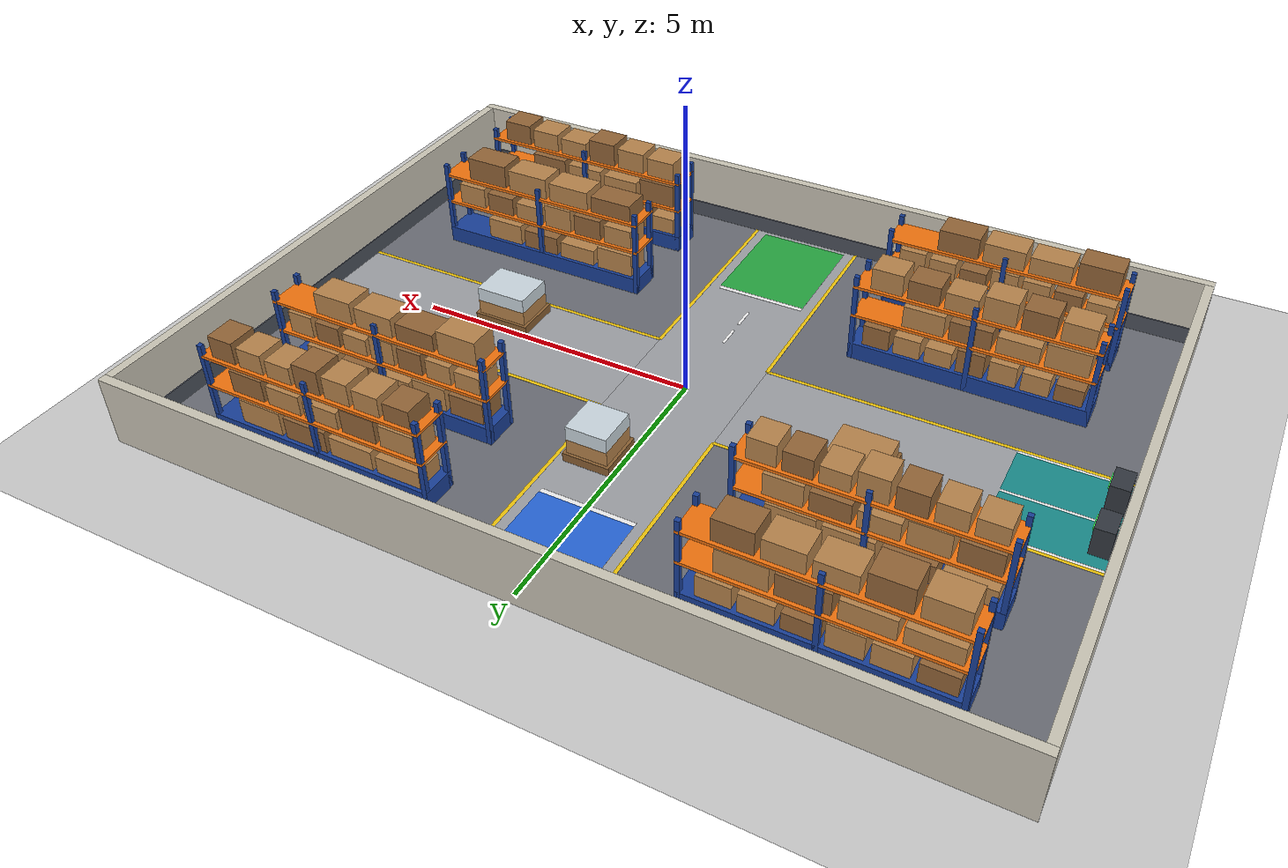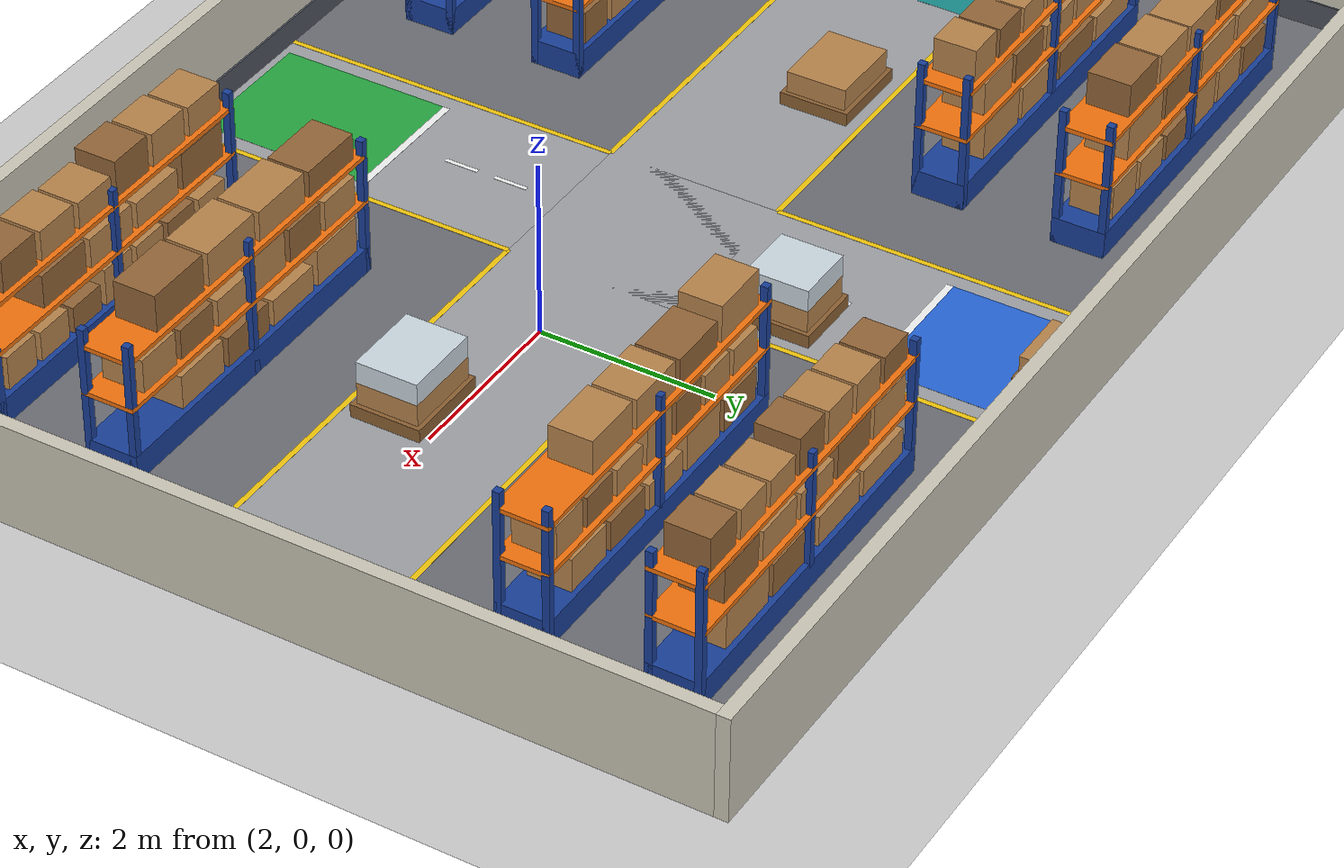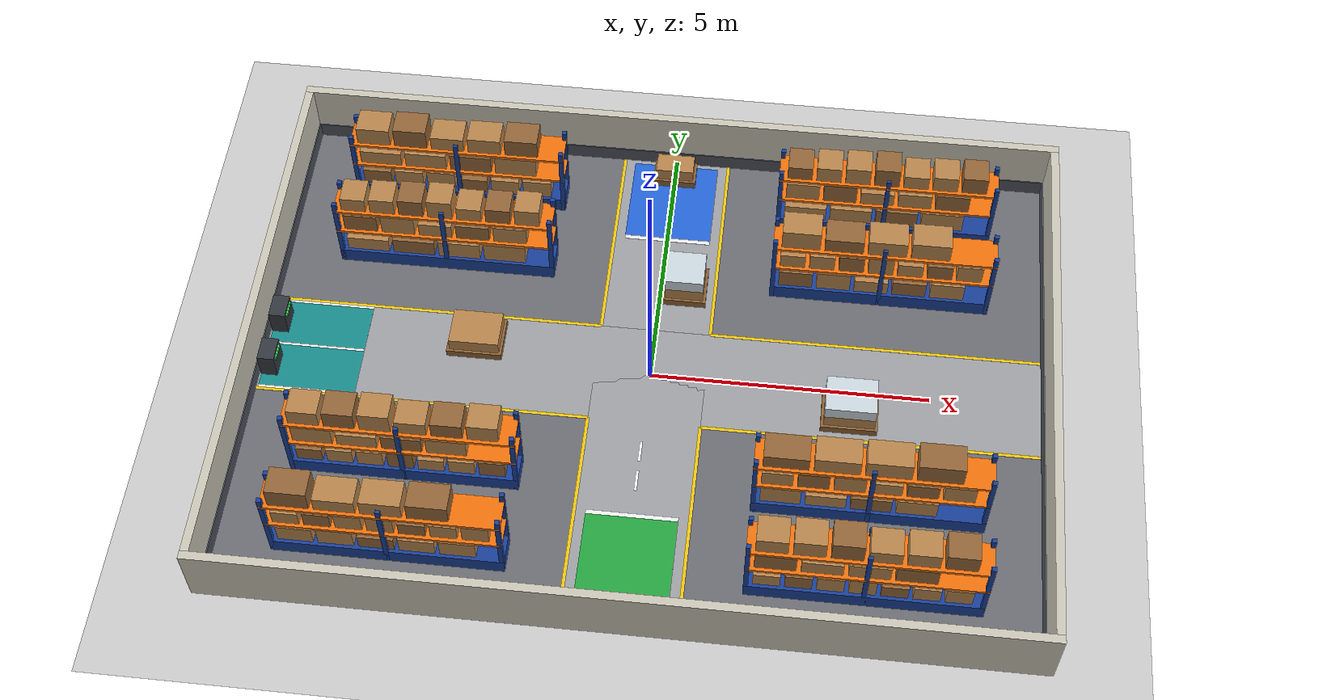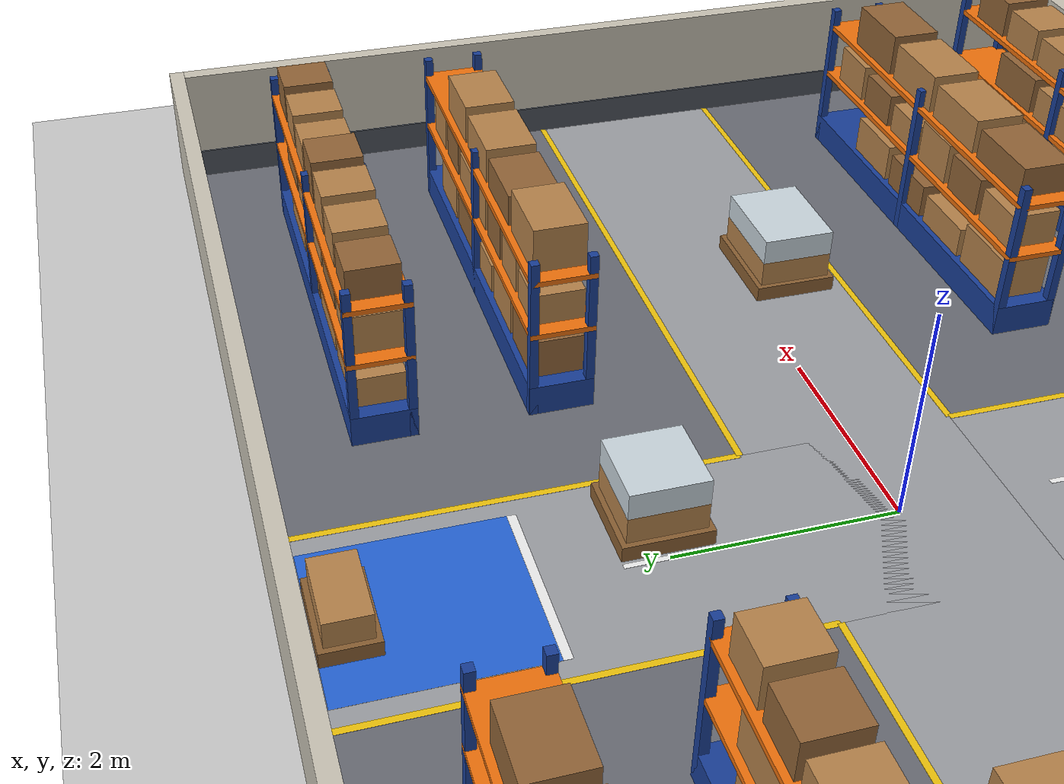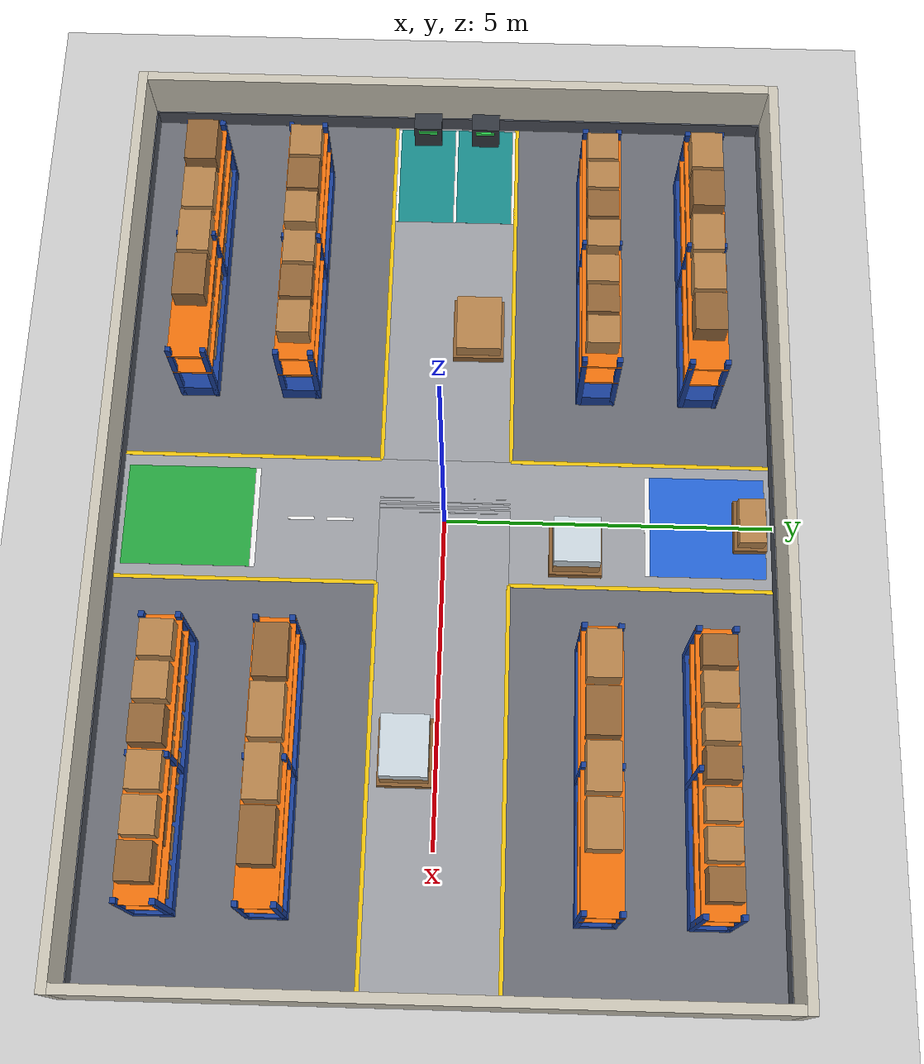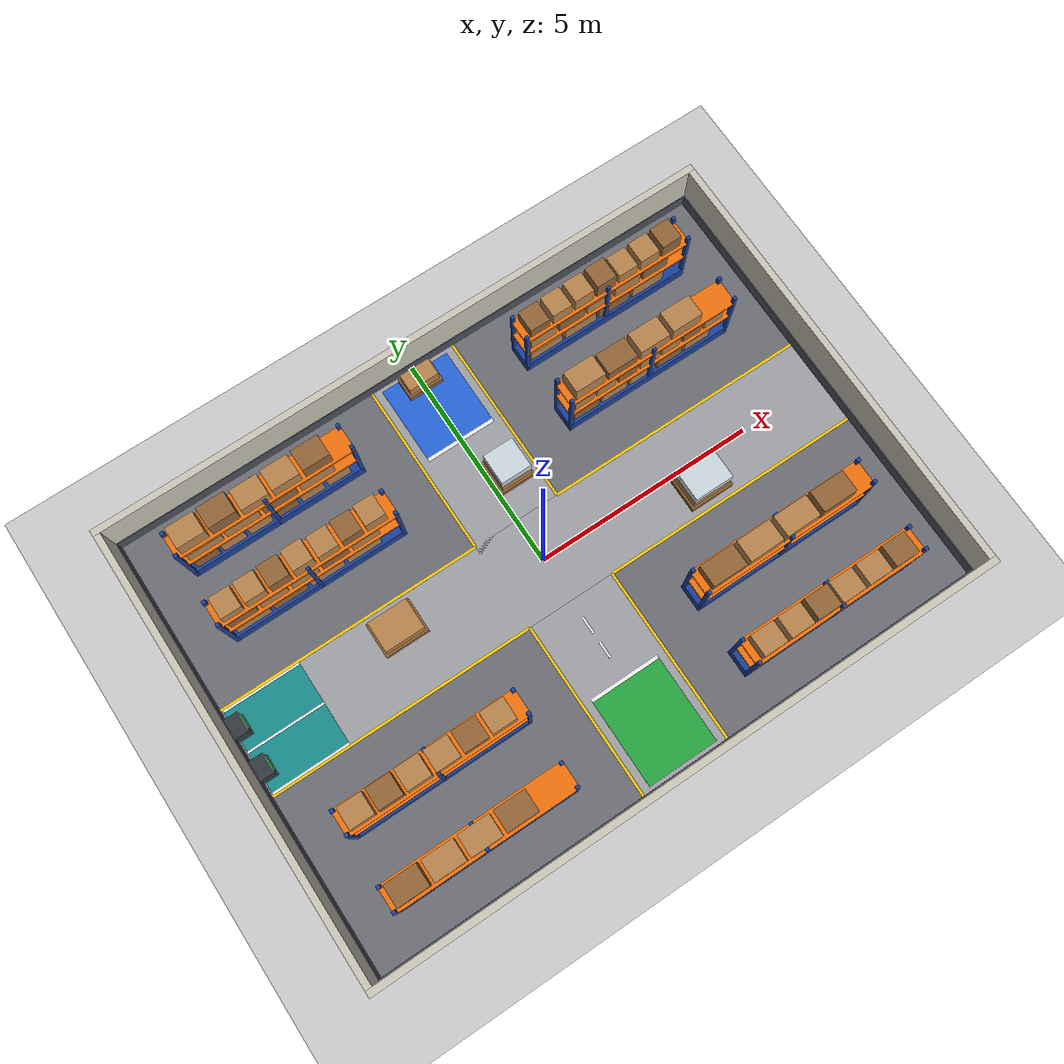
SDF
<?xml version="1.0"?>
<!-- GENERATED by tools/gen_amr_warehouse.py - edit the generator, not this file. -->
<sdf version="1.6">
  <world name="default">
    <include><uri>model://ground_plane</uri></include>
    <include><uri>model://sun</uri></include>
    <scene>
      <shadows>false</shadows>
      <ambient>0.55 0.55 0.55 1</ambient>
      <background>0.75 0.80 0.85 1</background>
    </scene>
    <gui fullscreen='0'>
      <camera name='user_camera'>
        <pose frame=''>0 -9.5 11.0 0 0.90 1.5708</pose>
        <view_controller>orbit</view_controller>
        <projection_type>perspective</projection_type>
      </camera>
    </gui>
    <physics type="ode">
      <real_time_update_rate>1000.0</real_time_update_rate>
      <max_step_size>0.001</max_step_size>
      <real_time_factor>1</real_time_factor>
      <ode>
        <solver><type>quick</type><iters>150</iters><precon_iters>0</precon_iters><sor>1.4</sor>
          <use_dynamic_moi_rescaling>1</use_dynamic_moi_rescaling></solver>
        <constraints><cfm>0.00001</cfm><erp>0.2</erp>
          <contact_max_correcting_vel>2000.0</contact_max_correcting_vel>
          <contact_surface_layer>0.01</contact_surface_layer></constraints>
      </ode>
    </physics>
    <model name="amr_warehouse">
      <static>true</static>
      <link name="floor_main_ns"><pose>0.000 0.000 0.001 0 0 0</pose><visual name="v"><geometry><box><size>2.000 10.000 0.002</size></box></geometry><material><ambient>0.62 0.63 0.65 1</ambient><diffuse>0.62 0.63 0.65 1</diffuse><specular>0.1 0.1 0.1 1</specular></material></visual></link>
      <link name="floor_cross_ew"><pose>0.000 0.000 0.001 0 0 0</pose><visual name="v"><geometry><box><size>14.000 2.000 0.002</size></box></geometry><material><ambient>0.62 0.63 0.65 1</ambient><diffuse>0.62 0.63 0.65 1</diffuse><specular>0.1 0.1 0.1 1</specular></material></visual></link>
      <link name="floor_storage_-1_-1"><pose>-4.000 -3.000 0.001 0 0 0</pose><visual name="v"><geometry><box><size>6.000 4.000 0.002</size></box></geometry><material><ambient>0.42 0.43 0.46 1</ambient><diffuse>0.42 0.43 0.46 1</diffuse><specular>0.1 0.1 0.1 1</specular></material></visual></link>
      <link name="floor_storage_-1_1"><pose>-4.000 3.000 0.001 0 0 0</pose><visual name="v"><geometry><box><size>6.000 4.000 0.002</size></box></geometry><material><ambient>0.42 0.43 0.46 1</ambient><diffuse>0.42 0.43 0.46 1</diffuse><specular>0.1 0.1 0.1 1</specular></material></visual></link>
      <link name="floor_storage_1_-1"><pose>4.000 -3.000 0.001 0 0 0</pose><visual name="v"><geometry><box><size>6.000 4.000 0.002</size></box></geometry><material><ambient>0.42 0.43 0.46 1</ambient><diffuse>0.42 0.43 0.46 1</diffuse><specular>0.1 0.1 0.1 1</specular></material></visual></link>
      <link name="floor_storage_1_1"><pose>4.000 3.000 0.001 0 0 0</pose><visual name="v"><geometry><box><size>6.000 4.000 0.002</size></box></geometry><material><ambient>0.42 0.43 0.46 1</ambient><diffuse>0.42 0.43 0.46 1</diffuse><specular>0.1 0.1 0.1 1</specular></material></visual></link>
      <link name="zone_start"><pose>0.000 -3.900 0.002 0 0 0</pose><visual name="v"><geometry><box><size>1.600 2.000 0.002</size></box></geometry><material><ambient>0.15 0.65 0.25 1</ambient><diffuse>0.15 0.65 0.25 1</diffuse><specular>0.1 0.1 0.1 1</specular></material></visual></link>
      <link name="zone_delivery"><pose>0.000 4.000 0.002 0 0 0</pose><visual name="v"><geometry><box><size>1.600 1.800 0.002</size></box></geometry><material><ambient>0.15 0.4 0.85 1</ambient><diffuse>0.15 0.4 0.85 1</diffuse><specular>0.1 0.1 0.1 1</specular></material></visual></link>
      <link name="zone_charge"><pose>-6.075 0.000 0.002 0 0 0</pose><visual name="v"><geometry><box><size>1.750 1.900 0.002</size></box></geometry><material><ambient>0.1 0.55 0.55 1</ambient><diffuse>0.1 0.55 0.55 1</diffuse><specular>0.1 0.1 0.1 1</specular></material></visual></link>
      <link name="mark_ns_s_-1"><pose>-1.000 -3.000 0.003 0 0 0</pose><visual name="v"><geometry><box><size>0.060 4.000 0.002</size></box></geometry><material><ambient>0.95 0.78 0.05 1</ambient><diffuse>0.95 0.78 0.05 1</diffuse><specular>0.1 0.1 0.1 1</specular></material></visual></link>
      <link name="mark_ns_n_-1"><pose>-1.000 3.000 0.003 0 0 0</pose><visual name="v"><geometry><box><size>0.060 4.000 0.002</size></box></geometry><material><ambient>0.95 0.78 0.05 1</ambient><diffuse>0.95 0.78 0.05 1</diffuse><specular>0.1 0.1 0.1 1</specular></material></visual></link>
      <link name="mark_ew_w_-1"><pose>-4.000 -1.000 0.003 0 0 0</pose><visual name="v"><geometry><box><size>6.000 0.060 0.002</size></box></geometry><material><ambient>0.95 0.78 0.05 1</ambient><diffuse>0.95 0.78 0.05 1</diffuse><specular>0.1 0.1 0.1 1</specular></material></visual></link>
      <link name="mark_ew_e_-1"><pose>4.000 -1.000 0.003 0 0 0</pose><visual name="v"><geometry><box><size>6.000 0.060 0.002</size></box></geometry><material><ambient>0.95 0.78 0.05 1</ambient><diffuse>0.95 0.78 0.05 1</diffuse><specular>0.1 0.1 0.1 1</specular></material></visual></link>
      <link name="mark_ns_s_1"><pose>1.000 -3.000 0.003 0 0 0</pose><visual name="v"><geometry><box><size>0.060 4.000 0.002</size></box></geometry><material><ambient>0.95 0.78 0.05 1</ambient><diffuse>0.95 0.78 0.05 1</diffuse><specular>0.1 0.1 0.1 1</specular></material></visual></link>
      <link name="mark_ns_n_1"><pose>1.000 3.000 0.003 0 0 0</pose><visual name="v"><geometry><box><size>0.060 4.000 0.002</size></box></geometry><material><ambient>0.95 0.78 0.05 1</ambient><diffuse>0.95 0.78 0.05 1</diffuse><specular>0.1 0.1 0.1 1</specular></material></visual></link>
      <link name="mark_ew_w_1"><pose>-4.000 1.000 0.003 0 0 0</pose><visual name="v"><geometry><box><size>6.000 0.060 0.002</size></box></geometry><material><ambient>0.95 0.78 0.05 1</ambient><diffuse>0.95 0.78 0.05 1</diffuse><specular>0.1 0.1 0.1 1</specular></material></visual></link>
      <link name="mark_ew_e_1"><pose>4.000 1.000 0.003 0 0 0</pose><visual name="v"><geometry><box><size>6.000 0.060 0.002</size></box></geometry><material><ambient>0.95 0.78 0.05 1</ambient><diffuse>0.95 0.78 0.05 1</diffuse><specular>0.1 0.1 0.1 1</specular></material></visual></link>
      <link name="mark_bay_0"><pose>-6.075 -0.950 0.003 0 0 0</pose><visual name="v"><geometry><box><size>1.750 0.050 0.002</size></box></geometry><material><ambient>0.95 0.95 0.95 1</ambient><diffuse>0.95 0.95 0.95 1</diffuse><specular>0.1 0.1 0.1 1</specular></material></visual></link>
      <link name="mark_bay_1"><pose>-6.075 0.000 0.003 0 0 0</pose><visual name="v"><geometry><box><size>1.750 0.050 0.002</size></box></geometry><material><ambient>0.95 0.95 0.95 1</ambient><diffuse>0.95 0.95 0.95 1</diffuse><specular>0.1 0.1 0.1 1</specular></material></visual></link>
      <link name="mark_bay_2"><pose>-6.075 0.950 0.003 0 0 0</pose><visual name="v"><geometry><box><size>1.750 0.050 0.002</size></box></geometry><material><ambient>0.95 0.95 0.95 1</ambient><diffuse>0.95 0.95 0.95 1</diffuse><specular>0.1 0.1 0.1 1</specular></material></visual></link>
      <link name="mark_stop_s"><pose>0.000 -2.900 0.003 0 0 0</pose><visual name="v"><geometry><box><size>1.600 0.080 0.002</size></box></geometry><material><ambient>0.95 0.95 0.95 1</ambient><diffuse>0.95 0.95 0.95 1</diffuse><specular>0.1 0.1 0.1 1</specular></material></visual></link>
      <link name="mark_stop_n"><pose>0.000 3.100 0.003 0 0 0</pose><visual name="v"><geometry><box><size>1.600 0.080 0.002</size></box></geometry><material><ambient>0.95 0.95 0.95 1</ambient><diffuse>0.95 0.95 0.95 1</diffuse><specular>0.1 0.1 0.1 1</specular></material></visual></link>
      <link name="mark_center_0"><pose>0.000 -2.200 0.003 0 0 0</pose><visual name="v"><geometry><box><size>0.050 0.400 0.002</size></box></geometry><material><ambient>0.95 0.95 0.95 1</ambient><diffuse>0.95 0.95 0.95 1</diffuse><specular>0.1 0.1 0.1 1</specular></material></visual></link>
      <link name="mark_center_1"><pose>0.000 -1.600 0.003 0 0 0</pose><visual name="v"><geometry><box><size>0.050 0.400 0.002</size></box></geometry><material><ambient>0.95 0.95 0.95 1</ambient><diffuse>0.95 0.95 0.95 1</diffuse><specular>0.1 0.1 0.1 1</specular></material></visual></link>
      <link name="mark_center_2"><pose>0.000 1.600 0.003 0 0 0</pose><visual name="v"><geometry><box><size>0.050 0.400 0.002</size></box></geometry><material><ambient>0.95 0.95 0.95 1</ambient><diffuse>0.95 0.95 0.95 1</diffuse><specular>0.1 0.1 0.1 1</specular></material></visual></link>
      <link name="mark_center_3"><pose>0.000 2.200 0.003 0 0 0</pose><visual name="v"><geometry><box><size>0.050 0.400 0.002</size></box></geometry><material><ambient>0.95 0.95 0.95 1</ambient><diffuse>0.95 0.95 0.95 1</diffuse><specular>0.1 0.1 0.1 1</specular></material></visual></link>
      <link name="wall_n"><pose>0.000 5.075 0.600 0 0 0</pose><collision name="c"><geometry><box><size>14.300 0.150 1.200</size></box></geometry></collision><visual name="v"><geometry><box><size>14.300 0.150 1.200</size></box></geometry><material><ambient>0.8 0.78 0.72 1</ambient><diffuse>0.8 0.78 0.72 1</diffuse><specular>0.1 0.1 0.1 1</specular></material></visual></link>
      <link name="wall_s"><pose>0.000 -5.075 0.600 0 0 0</pose><collision name="c"><geometry><box><size>14.300 0.150 1.200</size></box></geometry></collision><visual name="v"><geometry><box><size>14.300 0.150 1.200</size></box></geometry><material><ambient>0.8 0.78 0.72 1</ambient><diffuse>0.8 0.78 0.72 1</diffuse><specular>0.1 0.1 0.1 1</specular></material></visual></link>
      <link name="wall_e"><pose>7.075 0.000 0.600 0 0 0</pose><collision name="c"><geometry><box><size>0.150 10.000 1.200</size></box></geometry></collision><visual name="v"><geometry><box><size>0.150 10.000 1.200</size></box></geometry><material><ambient>0.8 0.78 0.72 1</ambient><diffuse>0.8 0.78 0.72 1</diffuse><specular>0.1 0.1 0.1 1</specular></material></visual></link>
      <link name="wall_w"><pose>-7.075 0.000 0.600 0 0 0</pose><collision name="c"><geometry><box><size>0.150 10.000 1.200</size></box></geometry></collision><visual name="v"><geometry><box><size>0.150 10.000 1.200</size></box></geometry><material><ambient>0.8 0.78 0.72 1</ambient><diffuse>0.8 0.78 0.72 1</diffuse><specular>0.1 0.1 0.1 1</specular></material></visual></link>
      <link name="wall_stripe0"><pose>0.000 4.990 0.150 0 0 0</pose><visual name="v"><geometry><box><size>14.000 0.020 0.300</size></box></geometry><material><ambient>0.3 0.32 0.36 1</ambient><diffuse>0.3 0.32 0.36 1</diffuse><specular>0.1 0.1 0.1 1</specular></material></visual></link>
      <link name="wall_stripe1"><pose>0.000 -4.990 0.150 0 0 0</pose><visual name="v"><geometry><box><size>14.000 0.020 0.300</size></box></geometry><material><ambient>0.3 0.32 0.36 1</ambient><diffuse>0.3 0.32 0.36 1</diffuse><specular>0.1 0.1 0.1 1</specular></material></visual></link>
      <link name="wall_stripe2"><pose>6.990 0.000 0.150 0 0 0</pose><visual name="v"><geometry><box><size>0.020 10.000 0.300</size></box></geometry><material><ambient>0.3 0.32 0.36 1</ambient><diffuse>0.3 0.32 0.36 1</diffuse><specular>0.1 0.1 0.1 1</specular></material></visual></link>
      <link name="wall_stripe3"><pose>-6.990 0.000 0.150 0 0 0</pose><visual name="v"><geometry><box><size>0.020 10.000 0.300</size></box></geometry><material><ambient>0.3 0.32 0.36 1</ambient><diffuse>0.3 0.32 0.36 1</diffuse><specular>0.1 0.1 0.1 1</specular></material></visual></link>
      <link name="rack_ES0_base"><pose>-4.000 -2.300 0.150 0 0 0</pose><collision name="c"><geometry><box><size>4.000 0.600 0.300</size></box></geometry></collision><visual name="v"><geometry><box><size>4.000 0.600 0.300</size></box></geometry><material><ambient>0.1 0.25 0.6 1</ambient><diffuse>0.1 0.25 0.6 1</diffuse><specular>0.1 0.1 0.1 1</specular></material></visual></link>
      <link name="rack_ES0_post00"><pose>-5.960 -2.560 0.800 0 0 0</pose><collision name="c"><geometry><box><size>0.080 0.080 1.600</size></box></geometry></collision><visual name="v"><geometry><box><size>0.080 0.080 1.600</size></box></geometry><material><ambient>0.1 0.25 0.6 1</ambient><diffuse>0.1 0.25 0.6 1</diffuse><specular>0.1 0.1 0.1 1</specular></material></visual></link>
      <link name="rack_ES0_post01"><pose>-5.960 -2.040 0.800 0 0 0</pose><collision name="c"><geometry><box><size>0.080 0.080 1.600</size></box></geometry></collision><visual name="v"><geometry><box><size>0.080 0.080 1.600</size></box></geometry><material><ambient>0.1 0.25 0.6 1</ambient><diffuse>0.1 0.25 0.6 1</diffuse><specular>0.1 0.1 0.1 1</specular></material></visual></link>
      <link name="rack_ES0_post10"><pose>-4.000 -2.560 0.800 0 0 0</pose><collision name="c"><geometry><box><size>0.080 0.080 1.600</size></box></geometry></collision><visual name="v"><geometry><box><size>0.080 0.080 1.600</size></box></geometry><material><ambient>0.1 0.25 0.6 1</ambient><diffuse>0.1 0.25 0.6 1</diffuse><specular>0.1 0.1 0.1 1</specular></material></visual></link>
      <link name="rack_ES0_post11"><pose>-4.000 -2.040 0.800 0 0 0</pose><collision name="c"><geometry><box><size>0.080 0.080 1.600</size></box></geometry></collision><visual name="v"><geometry><box><size>0.080 0.080 1.600</size></box></geometry><material><ambient>0.1 0.25 0.6 1</ambient><diffuse>0.1 0.25 0.6 1</diffuse><specular>0.1 0.1 0.1 1</specular></material></visual></link>
      <link name="rack_ES0_post20"><pose>-2.040 -2.560 0.800 0 0 0</pose><collision name="c"><geometry><box><size>0.080 0.080 1.600</size></box></geometry></collision><visual name="v"><geometry><box><size>0.080 0.080 1.600</size></box></geometry><material><ambient>0.1 0.25 0.6 1</ambient><diffuse>0.1 0.25 0.6 1</diffuse><specular>0.1 0.1 0.1 1</specular></material></visual></link>
      <link name="rack_ES0_post21"><pose>-2.040 -2.040 0.800 0 0 0</pose><collision name="c"><geometry><box><size>0.080 0.080 1.600</size></box></geometry></collision><visual name="v"><geometry><box><size>0.080 0.080 1.600</size></box></geometry><material><ambient>0.1 0.25 0.6 1</ambient><diffuse>0.1 0.25 0.6 1</diffuse><specular>0.1 0.1 0.1 1</specular></material></visual></link>
      <link name="rack_ES0_beam0"><pose>-4.000 -2.300 0.850 0 0 0</pose><collision name="c"><geometry><box><size>4.000 0.600 0.050</size></box></geometry></collision><visual name="v"><geometry><box><size>4.000 0.600 0.050</size></box></geometry><material><ambient>0.95 0.45 0.05 1</ambient><diffuse>0.95 0.45 0.05 1</diffuse><specular>0.1 0.1 0.1 1</specular></material></visual></link>
      <link name="rack_ES0_beam1"><pose>-4.000 -2.300 1.400 0 0 0</pose><collision name="c"><geometry><box><size>4.000 0.600 0.050</size></box></geometry></collision><visual name="v"><geometry><box><size>4.000 0.600 0.050</size></box></geometry><material><ambient>0.95 0.45 0.05 1</ambient><diffuse>0.95 0.45 0.05 1</diffuse><specular>0.1 0.1 0.1 1</specular></material></visual></link>
      <link name="rack_ES0_carton0_0"><pose>-5.625 -2.300 0.450 0 0 0</pose><visual name="v"><geometry><box><size>0.450 0.480 0.300</size></box></geometry><material><ambient>0.58 0.4 0.22 1</ambient><diffuse>0.58 0.4 0.22 1</diffuse><specular>0.1 0.1 0.1 1</specular></material></visual></link>
      <link name="rack_ES0_carton0_1"><pose>-5.095 -2.300 0.470 0 0 0</pose><visual name="v"><geometry><box><size>0.450 0.480 0.340</size></box></geometry><material><ambient>0.72 0.52 0.3 1</ambient><diffuse>0.72 0.52 0.3 1</diffuse><specular>0.1 0.1 0.1 1</specular></material></visual></link>
      <link name="rack_ES0_carton0_2"><pose>-4.565 -2.300 0.490 0 0 0</pose><visual name="v"><geometry><box><size>0.450 0.480 0.380</size></box></geometry><material><ambient>0.72 0.52 0.3 1</ambient><diffuse>0.72 0.52 0.3 1</diffuse><specular>0.1 0.1 0.1 1</specular></material></visual></link>
      <link name="rack_ES0_carton0_3"><pose>-4.035 -2.300 0.510 0 0 0</pose><visual name="v"><geometry><box><size>0.450 0.480 0.420</size></box></geometry><material><ambient>0.58 0.4 0.22 1</ambient><diffuse>0.58 0.4 0.22 1</diffuse><specular>0.1 0.1 0.1 1</specular></material></visual></link>
      <link name="rack_ES0_carton0_4"><pose>-3.505 -2.300 0.450 0 0 0</pose><visual name="v"><geometry><box><size>0.450 0.480 0.300</size></box></geometry><material><ambient>0.72 0.52 0.3 1</ambient><diffuse>0.72 0.52 0.3 1</diffuse><specular>0.1 0.1 0.1 1</specular></material></visual></link>
      <link name="rack_ES0_carton0_5"><pose>-2.975 -2.300 0.470 0 0 0</pose><visual name="v"><geometry><box><size>0.450 0.480 0.340</size></box></geometry><material><ambient>0.72 0.52 0.3 1</ambient><diffuse>0.72 0.52 0.3 1</diffuse><specular>0.1 0.1 0.1 1</specular></material></visual></link>
      <link name="rack_ES0_carton0_6"><pose>-2.445 -2.300 0.490 0 0 0</pose><visual name="v"><geometry><box><size>0.450 0.480 0.380</size></box></geometry><material><ambient>0.58 0.4 0.22 1</ambient><diffuse>0.58 0.4 0.22 1</diffuse><specular>0.1 0.1 0.1 1</specular></material></visual></link>
      <link name="rack_ES0_carton1_0"><pose>-5.505 -2.300 1.085 0 0 0</pose><visual name="v"><geometry><box><size>0.690 0.480 0.420</size></box></geometry><material><ambient>0.72 0.52 0.3 1</ambient><diffuse>0.72 0.52 0.3 1</diffuse><specular>0.1 0.1 0.1 1</specular></material></visual></link>
      <link name="rack_ES0_carton1_1"><pose>-4.735 -2.300 1.025 0 0 0</pose><visual name="v"><geometry><box><size>0.690 0.480 0.300</size></box></geometry><material><ambient>0.72 0.52 0.3 1</ambient><diffuse>0.72 0.52 0.3 1</diffuse><specular>0.1 0.1 0.1 1</specular></material></visual></link>
      <link name="rack_ES0_carton1_2"><pose>-3.965 -2.300 1.045 0 0 0</pose><visual name="v"><geometry><box><size>0.690 0.480 0.340</size></box></geometry><material><ambient>0.58 0.4 0.22 1</ambient><diffuse>0.58 0.4 0.22 1</diffuse><specular>0.1 0.1 0.1 1</specular></material></visual></link>
      <link name="rack_ES0_carton1_3"><pose>-3.195 -2.300 1.065 0 0 0</pose><visual name="v"><geometry><box><size>0.690 0.480 0.380</size></box></geometry><material><ambient>0.72 0.52 0.3 1</ambient><diffuse>0.72 0.52 0.3 1</diffuse><specular>0.1 0.1 0.1 1</specular></material></visual></link>
      <link name="rack_ES0_carton2_0"><pose>-5.585 -2.300 1.595 0 0 0</pose><visual name="v"><geometry><box><size>0.530 0.480 0.340</size></box></geometry><material><ambient>0.72 0.52 0.3 1</ambient><diffuse>0.72 0.52 0.3 1</diffuse><specular>0.1 0.1 0.1 1</specular></material></visual></link>
      <link name="rack_ES0_carton2_1"><pose>-4.975 -2.300 1.615 0 0 0</pose><visual name="v"><geometry><box><size>0.530 0.480 0.380</size></box></geometry><material><ambient>0.58 0.4 0.22 1</ambient><diffuse>0.58 0.4 0.22 1</diffuse><specular>0.1 0.1 0.1 1</specular></material></visual></link>
      <link name="rack_ES0_carton2_2"><pose>-4.365 -2.300 1.635 0 0 0</pose><visual name="v"><geometry><box><size>0.530 0.480 0.420</size></box></geometry><material><ambient>0.72 0.52 0.3 1</ambient><diffuse>0.72 0.52 0.3 1</diffuse><specular>0.1 0.1 0.1 1</specular></material></visual></link>
      <link name="rack_ES0_carton2_3"><pose>-3.755 -2.300 1.575 0 0 0</pose><visual name="v"><geometry><box><size>0.530 0.480 0.300</size></box></geometry><material><ambient>0.72 0.52 0.3 1</ambient><diffuse>0.72 0.52 0.3 1</diffuse><specular>0.1 0.1 0.1 1</specular></material></visual></link>
      <link name="rack_ES0_carton2_4"><pose>-3.145 -2.300 1.595 0 0 0</pose><visual name="v"><geometry><box><size>0.530 0.480 0.340</size></box></geometry><material><ambient>0.58 0.4 0.22 1</ambient><diffuse>0.58 0.4 0.22 1</diffuse><specular>0.1 0.1 0.1 1</specular></material></visual></link>
      <link name="rack_ES0_carton2_5"><pose>-2.535 -2.300 1.615 0 0 0</pose><visual name="v"><geometry><box><size>0.530 0.480 0.380</size></box></geometry><material><ambient>0.72 0.52 0.3 1</ambient><diffuse>0.72 0.52 0.3 1</diffuse><specular>0.1 0.1 0.1 1</specular></material></visual></link>
      <link name="rack_ES1_base"><pose>-4.000 -3.900 0.150 0 0 0</pose><collision name="c"><geometry><box><size>4.000 0.600 0.300</size></box></geometry></collision><visual name="v"><geometry><box><size>4.000 0.600 0.300</size></box></geometry><material><ambient>0.1 0.25 0.6 1</ambient><diffuse>0.1 0.25 0.6 1</diffuse><specular>0.1 0.1 0.1 1</specular></material></visual></link>
      <link name="rack_ES1_post00"><pose>-5.960 -4.160 0.800 0 0 0</pose><collision name="c"><geometry><box><size>0.080 0.080 1.600</size></box></geometry></collision><visual name="v"><geometry><box><size>0.080 0.080 1.600</size></box></geometry><material><ambient>0.1 0.25 0.6 1</ambient><diffuse>0.1 0.25 0.6 1</diffuse><specular>0.1 0.1 0.1 1</specular></material></visual></link>
      <link name="rack_ES1_post01"><pose>-5.960 -3.640 0.800 0 0 0</pose><collision name="c"><geometry><box><size>0.080 0.080 1.600</size></box></geometry></collision><visual name="v"><geometry><box><size>0.080 0.080 1.600</size></box></geometry><material><ambient>0.1 0.25 0.6 1</ambient><diffuse>0.1 0.25 0.6 1</diffuse><specular>0.1 0.1 0.1 1</specular></material></visual></link>
      <link name="rack_ES1_post10"><pose>-4.000 -4.160 0.800 0 0 0</pose><collision name="c"><geometry><box><size>0.080 0.080 1.600</size></box></geometry></collision><visual name="v"><geometry><box><size>0.080 0.080 1.600</size></box></geometry><material><ambient>0.1 0.25 0.6 1</ambient><diffuse>0.1 0.25 0.6 1</diffuse><specular>0.1 0.1 0.1 1</specular></material></visual></link>
      <link name="rack_ES1_post11"><pose>-4.000 -3.640 0.800 0 0 0</pose><collision name="c"><geometry><box><size>0.080 0.080 1.600</size></box></geometry></collision><visual name="v"><geometry><box><size>0.080 0.080 1.600</size></box></geometry><material><ambient>0.1 0.25 0.6 1</ambient><diffuse>0.1 0.25 0.6 1</diffuse><specular>0.1 0.1 0.1 1</specular></material></visual></link>
      <link name="rack_ES1_post20"><pose>-2.040 -4.160 0.800 0 0 0</pose><collision name="c"><geometry><box><size>0.080 0.080 1.600</size></box></geometry></collision><visual name="v"><geometry><box><size>0.080 0.080 1.600</size></box></geometry><material><ambient>0.1 0.25 0.6 1</ambient><diffuse>0.1 0.25 0.6 1</diffuse><specular>0.1 0.1 0.1 1</specular></material></visual></link>
      <link name="rack_ES1_post21"><pose>-2.040 -3.640 0.800 0 0 0</pose><collision name="c"><geometry><box><size>0.080 0.080 1.600</size></box></geometry></collision><visual name="v"><geometry><box><size>0.080 0.080 1.600</size></box></geometry><material><ambient>0.1 0.25 0.6 1</ambient><diffuse>0.1 0.25 0.6 1</diffuse><specular>0.1 0.1 0.1 1</specular></material></visual></link>
      <link name="rack_ES1_beam0"><pose>-4.000 -3.900 0.850 0 0 0</pose><collision name="c"><geometry><box><size>4.000 0.600 0.050</size></box></geometry></collision><visual name="v"><geometry><box><size>4.000 0.600 0.050</size></box></geometry><material><ambient>0.95 0.45 0.05 1</ambient><diffuse>0.95 0.45 0.05 1</diffuse><specular>0.1 0.1 0.1 1</specular></material></visual></link>
      <link name="rack_ES1_beam1"><pose>-4.000 -3.900 1.400 0 0 0</pose><collision name="c"><geometry><box><size>4.000 0.600 0.050</size></box></geometry></collision><visual name="v"><geometry><box><size>4.000 0.600 0.050</size></box></geometry><material><ambient>0.95 0.45 0.05 1</ambient><diffuse>0.95 0.45 0.05 1</diffuse><specular>0.1 0.1 0.1 1</specular></material></visual></link>
      <link name="rack_ES1_carton0_0"><pose>-5.545 -3.900 0.490 0 0 0</pose><visual name="v"><geometry><box><size>0.610 0.480 0.380</size></box></geometry><material><ambient>0.72 0.52 0.3 1</ambient><diffuse>0.72 0.52 0.3 1</diffuse><specular>0.1 0.1 0.1 1</specular></material></visual></link>
      <link name="rack_ES1_carton0_1"><pose>-4.855 -3.900 0.510 0 0 0</pose><visual name="v"><geometry><box><size>0.610 0.480 0.420</size></box></geometry><material><ambient>0.72 0.52 0.3 1</ambient><diffuse>0.72 0.52 0.3 1</diffuse><specular>0.1 0.1 0.1 1</specular></material></visual></link>
      <link name="rack_ES1_carton0_2"><pose>-4.165 -3.900 0.450 0 0 0</pose><visual name="v"><geometry><box><size>0.610 0.480 0.300</size></box></geometry><material><ambient>0.58 0.4 0.22 1</ambient><diffuse>0.58 0.4 0.22 1</diffuse><specular>0.1 0.1 0.1 1</specular></material></visual></link>
      <link name="rack_ES1_carton0_3"><pose>-3.475 -3.900 0.470 0 0 0</pose><visual name="v"><geometry><box><size>0.610 0.480 0.340</size></box></geometry><material><ambient>0.72 0.52 0.3 1</ambient><diffuse>0.72 0.52 0.3 1</diffuse><specular>0.1 0.1 0.1 1</specular></material></visual></link>
      <link name="rack_ES1_carton0_4"><pose>-2.785 -3.900 0.490 0 0 0</pose><visual name="v"><geometry><box><size>0.610 0.480 0.380</size></box></geometry><material><ambient>0.72 0.52 0.3 1</ambient><diffuse>0.72 0.52 0.3 1</diffuse><specular>0.1 0.1 0.1 1</specular></material></visual></link>
      <link name="rack_ES1_carton1_0"><pose>-5.625 -3.900 1.025 0 0 0</pose><visual name="v"><geometry><box><size>0.450 0.480 0.300</size></box></geometry><material><ambient>0.72 0.52 0.3 1</ambient><diffuse>0.72 0.52 0.3 1</diffuse><specular>0.1 0.1 0.1 1</specular></material></visual></link>
      <link name="rack_ES1_carton1_1"><pose>-5.095 -3.900 1.045 0 0 0</pose><visual name="v"><geometry><box><size>0.450 0.480 0.340</size></box></geometry><material><ambient>0.58 0.4 0.22 1</ambient><diffuse>0.58 0.4 0.22 1</diffuse><specular>0.1 0.1 0.1 1</specular></material></visual></link>
      <link name="rack_ES1_carton1_2"><pose>-4.565 -3.900 1.065 0 0 0</pose><visual name="v"><geometry><box><size>0.450 0.480 0.380</size></box></geometry><material><ambient>0.72 0.52 0.3 1</ambient><diffuse>0.72 0.52 0.3 1</diffuse><specular>0.1 0.1 0.1 1</specular></material></visual></link>
      <link name="rack_ES1_carton1_3"><pose>-4.035 -3.900 1.085 0 0 0</pose><visual name="v"><geometry><box><size>0.450 0.480 0.420</size></box></geometry><material><ambient>0.72 0.52 0.3 1</ambient><diffuse>0.72 0.52 0.3 1</diffuse><specular>0.1 0.1 0.1 1</specular></material></visual></link>
      <link name="rack_ES1_carton1_4"><pose>-3.505 -3.900 1.025 0 0 0</pose><visual name="v"><geometry><box><size>0.450 0.480 0.300</size></box></geometry><material><ambient>0.58 0.4 0.22 1</ambient><diffuse>0.58 0.4 0.22 1</diffuse><specular>0.1 0.1 0.1 1</specular></material></visual></link>
      <link name="rack_ES1_carton1_5"><pose>-2.975 -3.900 1.045 0 0 0</pose><visual name="v"><geometry><box><size>0.450 0.480 0.340</size></box></geometry><material><ambient>0.72 0.52 0.3 1</ambient><diffuse>0.72 0.52 0.3 1</diffuse><specular>0.1 0.1 0.1 1</specular></material></visual></link>
      <link name="rack_ES1_carton1_6"><pose>-2.445 -3.900 1.065 0 0 0</pose><visual name="v"><geometry><box><size>0.450 0.480 0.380</size></box></geometry><material><ambient>0.72 0.52 0.3 1</ambient><diffuse>0.72 0.52 0.3 1</diffuse><specular>0.1 0.1 0.1 1</specular></material></visual></link>
      <link name="rack_ES1_carton2_0"><pose>-5.505 -3.900 1.635 0 0 0</pose><visual name="v"><geometry><box><size>0.690 0.480 0.420</size></box></geometry><material><ambient>0.58 0.4 0.22 1</ambient><diffuse>0.58 0.4 0.22 1</diffuse><specular>0.1 0.1 0.1 1</specular></material></visual></link>
      <link name="rack_ES1_carton2_1"><pose>-4.735 -3.900 1.575 0 0 0</pose><visual name="v"><geometry><box><size>0.690 0.480 0.300</size></box></geometry><material><ambient>0.72 0.52 0.3 1</ambient><diffuse>0.72 0.52 0.3 1</diffuse><specular>0.1 0.1 0.1 1</specular></material></visual></link>
      <link name="rack_ES1_carton2_2"><pose>-3.965 -3.900 1.595 0 0 0</pose><visual name="v"><geometry><box><size>0.690 0.480 0.340</size></box></geometry><material><ambient>0.72 0.52 0.3 1</ambient><diffuse>0.72 0.52 0.3 1</diffuse><specular>0.1 0.1 0.1 1</specular></material></visual></link>
      <link name="rack_ES1_carton2_3"><pose>-3.195 -3.900 1.615 0 0 0</pose><visual name="v"><geometry><box><size>0.690 0.480 0.380</size></box></geometry><material><ambient>0.58 0.4 0.22 1</ambient><diffuse>0.58 0.4 0.22 1</diffuse><specular>0.1 0.1 0.1 1</specular></material></visual></link>
      <link name="rack_EN0_base"><pose>-4.000 2.300 0.150 0 0 0</pose><collision name="c"><geometry><box><size>4.000 0.600 0.300</size></box></geometry></collision><visual name="v"><geometry><box><size>4.000 0.600 0.300</size></box></geometry><material><ambient>0.1 0.25 0.6 1</ambient><diffuse>0.1 0.25 0.6 1</diffuse><specular>0.1 0.1 0.1 1</specular></material></visual></link>
      <link name="rack_EN0_post00"><pose>-5.960 2.040 0.800 0 0 0</pose><collision name="c"><geometry><box><size>0.080 0.080 1.600</size></box></geometry></collision><visual name="v"><geometry><box><size>0.080 0.080 1.600</size></box></geometry><material><ambient>0.1 0.25 0.6 1</ambient><diffuse>0.1 0.25 0.6 1</diffuse><specular>0.1 0.1 0.1 1</specular></material></visual></link>
      <link name="rack_EN0_post01"><pose>-5.960 2.560 0.800 0 0 0</pose><collision name="c"><geometry><box><size>0.080 0.080 1.600</size></box></geometry></collision><visual name="v"><geometry><box><size>0.080 0.080 1.600</size></box></geometry><material><ambient>0.1 0.25 0.6 1</ambient><diffuse>0.1 0.25 0.6 1</diffuse><specular>0.1 0.1 0.1 1</specular></material></visual></link>
      <link name="rack_EN0_post10"><pose>-4.000 2.040 0.800 0 0 0</pose><collision name="c"><geometry><box><size>0.080 0.080 1.600</size></box></geometry></collision><visual name="v"><geometry><box><size>0.080 0.080 1.600</size></box></geometry><material><ambient>0.1 0.25 0.6 1</ambient><diffuse>0.1 0.25 0.6 1</diffuse><specular>0.1 0.1 0.1 1</specular></material></visual></link>
      <link name="rack_EN0_post11"><pose>-4.000 2.560 0.800 0 0 0</pose><collision name="c"><geometry><box><size>0.080 0.080 1.600</size></box></geometry></collision><visual name="v"><geometry><box><size>0.080 0.080 1.600</size></box></geometry><material><ambient>0.1 0.25 0.6 1</ambient><diffuse>0.1 0.25 0.6 1</diffuse><specular>0.1 0.1 0.1 1</specular></material></visual></link>
      <link name="rack_EN0_post20"><pose>-2.040 2.040 0.800 0 0 0</pose><collision name="c"><geometry><box><size>0.080 0.080 1.600</size></box></geometry></collision><visual name="v"><geometry><box><size>0.080 0.080 1.600</size></box></geometry><material><ambient>0.1 0.25 0.6 1</ambient><diffuse>0.1 0.25 0.6 1</diffuse><specular>0.1 0.1 0.1 1</specular></material></visual></link>
      <link name="rack_EN0_post21"><pose>-2.040 2.560 0.800 0 0 0</pose><collision name="c"><geometry><box><size>0.080 0.080 1.600</size></box></geometry></collision><visual name="v"><geometry><box><size>0.080 0.080 1.600</size></box></geometry><material><ambient>0.1 0.25 0.6 1</ambient><diffuse>0.1 0.25 0.6 1</diffuse><specular>0.1 0.1 0.1 1</specular></material></visual></link>
      <link name="rack_EN0_beam0"><pose>-4.000 2.300 0.850 0 0 0</pose><collision name="c"><geometry><box><size>4.000 0.600 0.050</size></box></geometry></collision><visual name="v"><geometry><box><size>4.000 0.600 0.050</size></box></geometry><material><ambient>0.95 0.45 0.05 1</ambient><diffuse>0.95 0.45 0.05 1</diffuse><specular>0.1 0.1 0.1 1</specular></material></visual></link>
      <link name="rack_EN0_beam1"><pose>-4.000 2.300 1.400 0 0 0</pose><collision name="c"><geometry><box><size>4.000 0.600 0.050</size></box></geometry></collision><visual name="v"><geometry><box><size>4.000 0.600 0.050</size></box></geometry><material><ambient>0.95 0.45 0.05 1</ambient><diffuse>0.95 0.45 0.05 1</diffuse><specular>0.1 0.1 0.1 1</specular></material></visual></link>
      <link name="rack_EN0_carton0_0"><pose>-5.465 2.300 0.450 0 0 0</pose><visual name="v"><geometry><box><size>0.770 0.480 0.300</size></box></geometry><material><ambient>0.72 0.52 0.3 1</ambient><diffuse>0.72 0.52 0.3 1</diffuse><specular>0.1 0.1 0.1 1</specular></material></visual></link>
      <link name="rack_EN0_carton0_1"><pose>-4.615 2.300 0.470 0 0 0</pose><visual name="v"><geometry><box><size>0.770 0.480 0.340</size></box></geometry><material><ambient>0.58 0.4 0.22 1</ambient><diffuse>0.58 0.4 0.22 1</diffuse><specular>0.1 0.1 0.1 1</specular></material></visual></link>
      <link name="rack_EN0_carton0_2"><pose>-3.765 2.300 0.490 0 0 0</pose><visual name="v"><geometry><box><size>0.770 0.480 0.380</size></box></geometry><material><ambient>0.72 0.52 0.3 1</ambient><diffuse>0.72 0.52 0.3 1</diffuse><specular>0.1 0.1 0.1 1</specular></material></visual></link>
      <link name="rack_EN0_carton0_3"><pose>-2.915 2.300 0.510 0 0 0</pose><visual name="v"><geometry><box><size>0.770 0.480 0.420</size></box></geometry><material><ambient>0.72 0.52 0.3 1</ambient><diffuse>0.72 0.52 0.3 1</diffuse><specular>0.1 0.1 0.1 1</specular></material></visual></link>
      <link name="rack_EN0_carton1_0"><pose>-5.545 2.300 1.065 0 0 0</pose><visual name="v"><geometry><box><size>0.610 0.480 0.380</size></box></geometry><material><ambient>0.58 0.4 0.22 1</ambient><diffuse>0.58 0.4 0.22 1</diffuse><specular>0.1 0.1 0.1 1</specular></material></visual></link>
      <link name="rack_EN0_carton1_1"><pose>-4.855 2.300 1.085 0 0 0</pose><visual name="v"><geometry><box><size>0.610 0.480 0.420</size></box></geometry><material><ambient>0.72 0.52 0.3 1</ambient><diffuse>0.72 0.52 0.3 1</diffuse><specular>0.1 0.1 0.1 1</specular></material></visual></link>
      <link name="rack_EN0_carton1_2"><pose>-4.165 2.300 1.025 0 0 0</pose><visual name="v"><geometry><box><size>0.610 0.480 0.300</size></box></geometry><material><ambient>0.72 0.52 0.3 1</ambient><diffuse>0.72 0.52 0.3 1</diffuse><specular>0.1 0.1 0.1 1</specular></material></visual></link>
      <link name="rack_EN0_carton1_3"><pose>-3.475 2.300 1.045 0 0 0</pose><visual name="v"><geometry><box><size>0.610 0.480 0.340</size></box></geometry><material><ambient>0.58 0.4 0.22 1</ambient><diffuse>0.58 0.4 0.22 1</diffuse><specular>0.1 0.1 0.1 1</specular></material></visual></link>
      <link name="rack_EN0_carton1_4"><pose>-2.785 2.300 1.065 0 0 0</pose><visual name="v"><geometry><box><size>0.610 0.480 0.380</size></box></geometry><material><ambient>0.72 0.52 0.3 1</ambient><diffuse>0.72 0.52 0.3 1</diffuse><specular>0.1 0.1 0.1 1</specular></material></visual></link>
      <link name="rack_EN0_carton2_0"><pose>-5.625 2.300 1.575 0 0 0</pose><visual name="v"><geometry><box><size>0.450 0.480 0.300</size></box></geometry><material><ambient>0.72 0.52 0.3 1</ambient><diffuse>0.72 0.52 0.3 1</diffuse><specular>0.1 0.1 0.1 1</specular></material></visual></link>
      <link name="rack_EN0_carton2_1"><pose>-5.095 2.300 1.595 0 0 0</pose><visual name="v"><geometry><box><size>0.450 0.480 0.340</size></box></geometry><material><ambient>0.72 0.52 0.3 1</ambient><diffuse>0.72 0.52 0.3 1</diffuse><specular>0.1 0.1 0.1 1</specular></material></visual></link>
      <link name="rack_EN0_carton2_2"><pose>-4.565 2.300 1.615 0 0 0</pose><visual name="v"><geometry><box><size>0.450 0.480 0.380</size></box></geometry><material><ambient>0.58 0.4 0.22 1</ambient><diffuse>0.58 0.4 0.22 1</diffuse><specular>0.1 0.1 0.1 1</specular></material></visual></link>
      <link name="rack_EN0_carton2_3"><pose>-4.035 2.300 1.635 0 0 0</pose><visual name="v"><geometry><box><size>0.450 0.480 0.420</size></box></geometry><material><ambient>0.72 0.52 0.3 1</ambient><diffuse>0.72 0.52 0.3 1</diffuse><specular>0.1 0.1 0.1 1</specular></material></visual></link>
      <link name="rack_EN0_carton2_4"><pose>-3.505 2.300 1.575 0 0 0</pose><visual name="v"><geometry><box><size>0.450 0.480 0.300</size></box></geometry><material><ambient>0.72 0.52 0.3 1</ambient><diffuse>0.72 0.52 0.3 1</diffuse><specular>0.1 0.1 0.1 1</specular></material></visual></link>
      <link name="rack_EN0_carton2_5"><pose>-2.975 2.300 1.595 0 0 0</pose><visual name="v"><geometry><box><size>0.450 0.480 0.340</size></box></geometry><material><ambient>0.58 0.4 0.22 1</ambient><diffuse>0.58 0.4 0.22 1</diffuse><specular>0.1 0.1 0.1 1</specular></material></visual></link>
      <link name="rack_EN0_carton2_6"><pose>-2.445 2.300 1.615 0 0 0</pose><visual name="v"><geometry><box><size>0.450 0.480 0.380</size></box></geometry><material><ambient>0.72 0.52 0.3 1</ambient><diffuse>0.72 0.52 0.3 1</diffuse><specular>0.1 0.1 0.1 1</specular></material></visual></link>
      <link name="rack_EN1_base"><pose>-4.000 3.900 0.150 0 0 0</pose><collision name="c"><geometry><box><size>4.000 0.600 0.300</size></box></geometry></collision><visual name="v"><geometry><box><size>4.000 0.600 0.300</size></box></geometry><material><ambient>0.1 0.25 0.6 1</ambient><diffuse>0.1 0.25 0.6 1</diffuse><specular>0.1 0.1 0.1 1</specular></material></visual></link>
      <link name="rack_EN1_post00"><pose>-5.960 3.640 0.800 0 0 0</pose><collision name="c"><geometry><box><size>0.080 0.080 1.600</size></box></geometry></collision><visual name="v"><geometry><box><size>0.080 0.080 1.600</size></box></geometry><material><ambient>0.1 0.25 0.6 1</ambient><diffuse>0.1 0.25 0.6 1</diffuse><specular>0.1 0.1 0.1 1</specular></material></visual></link>
      <link name="rack_EN1_post01"><pose>-5.960 4.160 0.800 0 0 0</pose><collision name="c"><geometry><box><size>0.080 0.080 1.600</size></box></geometry></collision><visual name="v"><geometry><box><size>0.080 0.080 1.600</size></box></geometry><material><ambient>0.1 0.25 0.6 1</ambient><diffuse>0.1 0.25 0.6 1</diffuse><specular>0.1 0.1 0.1 1</specular></material></visual></link>
      <link name="rack_EN1_post10"><pose>-4.000 3.640 0.800 0 0 0</pose><collision name="c"><geometry><box><size>0.080 0.080 1.600</size></box></geometry></collision><visual name="v"><geometry><box><size>0.080 0.080 1.600</size></box></geometry><material><ambient>0.1 0.25 0.6 1</ambient><diffuse>0.1 0.25 0.6 1</diffuse><specular>0.1 0.1 0.1 1</specular></material></visual></link>
      <link name="rack_EN1_post11"><pose>-4.000 4.160 0.800 0 0 0</pose><collision name="c"><geometry><box><size>0.080 0.080 1.600</size></box></geometry></collision><visual name="v"><geometry><box><size>0.080 0.080 1.600</size></box></geometry><material><ambient>0.1 0.25 0.6 1</ambient><diffuse>0.1 0.25 0.6 1</diffuse><specular>0.1 0.1 0.1 1</specular></material></visual></link>
      <link name="rack_EN1_post20"><pose>-2.040 3.640 0.800 0 0 0</pose><collision name="c"><geometry><box><size>0.080 0.080 1.600</size></box></geometry></collision><visual name="v"><geometry><box><size>0.080 0.080 1.600</size></box></geometry><material><ambient>0.1 0.25 0.6 1</ambient><diffuse>0.1 0.25 0.6 1</diffuse><specular>0.1 0.1 0.1 1</specular></material></visual></link>
      <link name="rack_EN1_post21"><pose>-2.040 4.160 0.800 0 0 0</pose><collision name="c"><geometry><box><size>0.080 0.080 1.600</size></box></geometry></collision><visual name="v"><geometry><box><size>0.080 0.080 1.600</size></box></geometry><material><ambient>0.1 0.25 0.6 1</ambient><diffuse>0.1 0.25 0.6 1</diffuse><specular>0.1 0.1 0.1 1</specular></material></visual></link>
      <link name="rack_EN1_beam0"><pose>-4.000 3.900 0.850 0 0 0</pose><collision name="c"><geometry><box><size>4.000 0.600 0.050</size></box></geometry></collision><visual name="v"><geometry><box><size>4.000 0.600 0.050</size></box></geometry><material><ambient>0.95 0.45 0.05 1</ambient><diffuse>0.95 0.45 0.05 1</diffuse><specular>0.1 0.1 0.1 1</specular></material></visual></link>
      <link name="rack_EN1_beam1"><pose>-4.000 3.900 1.400 0 0 0</pose><collision name="c"><geometry><box><size>4.000 0.600 0.050</size></box></geometry></collision><visual name="v"><geometry><box><size>4.000 0.600 0.050</size></box></geometry><material><ambient>0.95 0.45 0.05 1</ambient><diffuse>0.95 0.45 0.05 1</diffuse><specular>0.1 0.1 0.1 1</specular></material></visual></link>
      <link name="rack_EN1_carton0_0"><pose>-5.585 3.900 0.470 0 0 0</pose><visual name="v"><geometry><box><size>0.530 0.480 0.340</size></box></geometry><material><ambient>0.58 0.4 0.22 1</ambient><diffuse>0.58 0.4 0.22 1</diffuse><specular>0.1 0.1 0.1 1</specular></material></visual></link>
      <link name="rack_EN1_carton0_1"><pose>-4.975 3.900 0.490 0 0 0</pose><visual name="v"><geometry><box><size>0.530 0.480 0.380</size></box></geometry><material><ambient>0.72 0.52 0.3 1</ambient><diffuse>0.72 0.52 0.3 1</diffuse><specular>0.1 0.1 0.1 1</specular></material></visual></link>
      <link name="rack_EN1_carton0_2"><pose>-4.365 3.900 0.510 0 0 0</pose><visual name="v"><geometry><box><size>0.530 0.480 0.420</size></box></geometry><material><ambient>0.72 0.52 0.3 1</ambient><diffuse>0.72 0.52 0.3 1</diffuse><specular>0.1 0.1 0.1 1</specular></material></visual></link>
      <link name="rack_EN1_carton0_3"><pose>-3.755 3.900 0.450 0 0 0</pose><visual name="v"><geometry><box><size>0.530 0.480 0.300</size></box></geometry><material><ambient>0.58 0.4 0.22 1</ambient><diffuse>0.58 0.4 0.22 1</diffuse><specular>0.1 0.1 0.1 1</specular></material></visual></link>
      <link name="rack_EN1_carton0_4"><pose>-3.145 3.900 0.470 0 0 0</pose><visual name="v"><geometry><box><size>0.530 0.480 0.340</size></box></geometry><material><ambient>0.72 0.52 0.3 1</ambient><diffuse>0.72 0.52 0.3 1</diffuse><specular>0.1 0.1 0.1 1</specular></material></visual></link>
      <link name="rack_EN1_carton0_5"><pose>-2.535 3.900 0.490 0 0 0</pose><visual name="v"><geometry><box><size>0.530 0.480 0.380</size></box></geometry><material><ambient>0.72 0.52 0.3 1</ambient><diffuse>0.72 0.52 0.3 1</diffuse><specular>0.1 0.1 0.1 1</specular></material></visual></link>
      <link name="rack_EN1_carton1_0"><pose>-5.465 3.900 1.025 0 0 0</pose><visual name="v"><geometry><box><size>0.770 0.480 0.300</size></box></geometry><material><ambient>0.72 0.52 0.3 1</ambient><diffuse>0.72 0.52 0.3 1</diffuse><specular>0.1 0.1 0.1 1</specular></material></visual></link>
      <link name="rack_EN1_carton1_1"><pose>-4.615 3.900 1.045 0 0 0</pose><visual name="v"><geometry><box><size>0.770 0.480 0.340</size></box></geometry><material><ambient>0.72 0.52 0.3 1</ambient><diffuse>0.72 0.52 0.3 1</diffuse><specular>0.1 0.1 0.1 1</specular></material></visual></link>
      <link name="rack_EN1_carton1_2"><pose>-3.765 3.900 1.065 0 0 0</pose><visual name="v"><geometry><box><size>0.770 0.480 0.380</size></box></geometry><material><ambient>0.58 0.4 0.22 1</ambient><diffuse>0.58 0.4 0.22 1</diffuse><specular>0.1 0.1 0.1 1</specular></material></visual></link>
      <link name="rack_EN1_carton1_3"><pose>-2.915 3.900 1.085 0 0 0</pose><visual name="v"><geometry><box><size>0.770 0.480 0.420</size></box></geometry><material><ambient>0.72 0.52 0.3 1</ambient><diffuse>0.72 0.52 0.3 1</diffuse><specular>0.1 0.1 0.1 1</specular></material></visual></link>
      <link name="rack_EN1_carton2_0"><pose>-5.545 3.900 1.615 0 0 0</pose><visual name="v"><geometry><box><size>0.610 0.480 0.380</size></box></geometry><material><ambient>0.72 0.52 0.3 1</ambient><diffuse>0.72 0.52 0.3 1</diffuse><specular>0.1 0.1 0.1 1</specular></material></visual></link>
      <link name="rack_EN1_carton2_1"><pose>-4.855 3.900 1.635 0 0 0</pose><visual name="v"><geometry><box><size>0.610 0.480 0.420</size></box></geometry><material><ambient>0.58 0.4 0.22 1</ambient><diffuse>0.58 0.4 0.22 1</diffuse><specular>0.1 0.1 0.1 1</specular></material></visual></link>
      <link name="rack_EN1_carton2_2"><pose>-4.165 3.900 1.575 0 0 0</pose><visual name="v"><geometry><box><size>0.610 0.480 0.300</size></box></geometry><material><ambient>0.72 0.52 0.3 1</ambient><diffuse>0.72 0.52 0.3 1</diffuse><specular>0.1 0.1 0.1 1</specular></material></visual></link>
      <link name="rack_EN1_carton2_3"><pose>-3.475 3.900 1.595 0 0 0</pose><visual name="v"><geometry><box><size>0.610 0.480 0.340</size></box></geometry><material><ambient>0.72 0.52 0.3 1</ambient><diffuse>0.72 0.52 0.3 1</diffuse><specular>0.1 0.1 0.1 1</specular></material></visual></link>
      <link name="rack_EN1_carton2_4"><pose>-2.785 3.900 1.615 0 0 0</pose><visual name="v"><geometry><box><size>0.610 0.480 0.380</size></box></geometry><material><ambient>0.58 0.4 0.22 1</ambient><diffuse>0.58 0.4 0.22 1</diffuse><specular>0.1 0.1 0.1 1</specular></material></visual></link>
      <link name="rack_WS0_base"><pose>4.000 -2.300 0.150 0 0 0</pose><collision name="c"><geometry><box><size>4.000 0.600 0.300</size></box></geometry></collision><visual name="v"><geometry><box><size>4.000 0.600 0.300</size></box></geometry><material><ambient>0.1 0.25 0.6 1</ambient><diffuse>0.1 0.25 0.6 1</diffuse><specular>0.1 0.1 0.1 1</specular></material></visual></link>
      <link name="rack_WS0_post00"><pose>2.040 -2.560 0.800 0 0 0</pose><collision name="c"><geometry><box><size>0.080 0.080 1.600</size></box></geometry></collision><visual name="v"><geometry><box><size>0.080 0.080 1.600</size></box></geometry><material><ambient>0.1 0.25 0.6 1</ambient><diffuse>0.1 0.25 0.6 1</diffuse><specular>0.1 0.1 0.1 1</specular></material></visual></link>
      <link name="rack_WS0_post01"><pose>2.040 -2.040 0.800 0 0 0</pose><collision name="c"><geometry><box><size>0.080 0.080 1.600</size></box></geometry></collision><visual name="v"><geometry><box><size>0.080 0.080 1.600</size></box></geometry><material><ambient>0.1 0.25 0.6 1</ambient><diffuse>0.1 0.25 0.6 1</diffuse><specular>0.1 0.1 0.1 1</specular></material></visual></link>
      <link name="rack_WS0_post10"><pose>4.000 -2.560 0.800 0 0 0</pose><collision name="c"><geometry><box><size>0.080 0.080 1.600</size></box></geometry></collision><visual name="v"><geometry><box><size>0.080 0.080 1.600</size></box></geometry><material><ambient>0.1 0.25 0.6 1</ambient><diffuse>0.1 0.25 0.6 1</diffuse><specular>0.1 0.1 0.1 1</specular></material></visual></link>
      <link name="rack_WS0_post11"><pose>4.000 -2.040 0.800 0 0 0</pose><collision name="c"><geometry><box><size>0.080 0.080 1.600</size></box></geometry></collision><visual name="v"><geometry><box><size>0.080 0.080 1.600</size></box></geometry><material><ambient>0.1 0.25 0.6 1</ambient><diffuse>0.1 0.25 0.6 1</diffuse><specular>0.1 0.1 0.1 1</specular></material></visual></link>
      <link name="rack_WS0_post20"><pose>5.960 -2.560 0.800 0 0 0</pose><collision name="c"><geometry><box><size>0.080 0.080 1.600</size></box></geometry></collision><visual name="v"><geometry><box><size>0.080 0.080 1.600</size></box></geometry><material><ambient>0.1 0.25 0.6 1</ambient><diffuse>0.1 0.25 0.6 1</diffuse><specular>0.1 0.1 0.1 1</specular></material></visual></link>
      <link name="rack_WS0_post21"><pose>5.960 -2.040 0.800 0 0 0</pose><collision name="c"><geometry><box><size>0.080 0.080 1.600</size></box></geometry></collision><visual name="v"><geometry><box><size>0.080 0.080 1.600</size></box></geometry><material><ambient>0.1 0.25 0.6 1</ambient><diffuse>0.1 0.25 0.6 1</diffuse><specular>0.1 0.1 0.1 1</specular></material></visual></link>
      <link name="rack_WS0_beam0"><pose>4.000 -2.300 0.850 0 0 0</pose><collision name="c"><geometry><box><size>4.000 0.600 0.050</size></box></geometry></collision><visual name="v"><geometry><box><size>4.000 0.600 0.050</size></box></geometry><material><ambient>0.95 0.45 0.05 1</ambient><diffuse>0.95 0.45 0.05 1</diffuse><specular>0.1 0.1 0.1 1</specular></material></visual></link>
      <link name="rack_WS0_beam1"><pose>4.000 -2.300 1.400 0 0 0</pose><collision name="c"><geometry><box><size>4.000 0.600 0.050</size></box></geometry></collision><visual name="v"><geometry><box><size>4.000 0.600 0.050</size></box></geometry><material><ambient>0.95 0.45 0.05 1</ambient><diffuse>0.95 0.45 0.05 1</diffuse><specular>0.1 0.1 0.1 1</specular></material></visual></link>
      <link name="rack_WS0_carton0_0"><pose>2.495 -2.300 0.510 0 0 0</pose><visual name="v"><geometry><box><size>0.690 0.480 0.420</size></box></geometry><material><ambient>0.72 0.52 0.3 1</ambient><diffuse>0.72 0.52 0.3 1</diffuse><specular>0.1 0.1 0.1 1</specular></material></visual></link>
      <link name="rack_WS0_carton0_1"><pose>3.265 -2.300 0.450 0 0 0</pose><visual name="v"><geometry><box><size>0.690 0.480 0.300</size></box></geometry><material><ambient>0.72 0.52 0.3 1</ambient><diffuse>0.72 0.52 0.3 1</diffuse><specular>0.1 0.1 0.1 1</specular></material></visual></link>
      <link name="rack_WS0_carton0_2"><pose>4.035 -2.300 0.470 0 0 0</pose><visual name="v"><geometry><box><size>0.690 0.480 0.340</size></box></geometry><material><ambient>0.58 0.4 0.22 1</ambient><diffuse>0.58 0.4 0.22 1</diffuse><specular>0.1 0.1 0.1 1</specular></material></visual></link>
      <link name="rack_WS0_carton0_3"><pose>4.805 -2.300 0.490 0 0 0</pose><visual name="v"><geometry><box><size>0.690 0.480 0.380</size></box></geometry><material><ambient>0.72 0.52 0.3 1</ambient><diffuse>0.72 0.52 0.3 1</diffuse><specular>0.1 0.1 0.1 1</specular></material></visual></link>
      <link name="rack_WS0_carton1_0"><pose>2.415 -2.300 1.045 0 0 0</pose><visual name="v"><geometry><box><size>0.530 0.480 0.340</size></box></geometry><material><ambient>0.72 0.52 0.3 1</ambient><diffuse>0.72 0.52 0.3 1</diffuse><specular>0.1 0.1 0.1 1</specular></material></visual></link>
      <link name="rack_WS0_carton1_1"><pose>3.025 -2.300 1.065 0 0 0</pose><visual name="v"><geometry><box><size>0.530 0.480 0.380</size></box></geometry><material><ambient>0.58 0.4 0.22 1</ambient><diffuse>0.58 0.4 0.22 1</diffuse><specular>0.1 0.1 0.1 1</specular></material></visual></link>
      <link name="rack_WS0_carton1_2"><pose>3.635 -2.300 1.085 0 0 0</pose><visual name="v"><geometry><box><size>0.530 0.480 0.420</size></box></geometry><material><ambient>0.72 0.52 0.3 1</ambient><diffuse>0.72 0.52 0.3 1</diffuse><specular>0.1 0.1 0.1 1</specular></material></visual></link>
      <link name="rack_WS0_carton1_3"><pose>4.245 -2.300 1.025 0 0 0</pose><visual name="v"><geometry><box><size>0.530 0.480 0.300</size></box></geometry><material><ambient>0.72 0.52 0.3 1</ambient><diffuse>0.72 0.52 0.3 1</diffuse><specular>0.1 0.1 0.1 1</specular></material></visual></link>
      <link name="rack_WS0_carton1_4"><pose>4.855 -2.300 1.045 0 0 0</pose><visual name="v"><geometry><box><size>0.530 0.480 0.340</size></box></geometry><material><ambient>0.58 0.4 0.22 1</ambient><diffuse>0.58 0.4 0.22 1</diffuse><specular>0.1 0.1 0.1 1</specular></material></visual></link>
      <link name="rack_WS0_carton1_5"><pose>5.465 -2.300 1.065 0 0 0</pose><visual name="v"><geometry><box><size>0.530 0.480 0.380</size></box></geometry><material><ambient>0.72 0.52 0.3 1</ambient><diffuse>0.72 0.52 0.3 1</diffuse><specular>0.1 0.1 0.1 1</specular></material></visual></link>
      <link name="rack_WS0_carton2_0"><pose>2.535 -2.300 1.575 0 0 0</pose><visual name="v"><geometry><box><size>0.770 0.480 0.300</size></box></geometry><material><ambient>0.58 0.4 0.22 1</ambient><diffuse>0.58 0.4 0.22 1</diffuse><specular>0.1 0.1 0.1 1</specular></material></visual></link>
      <link name="rack_WS0_carton2_1"><pose>3.385 -2.300 1.595 0 0 0</pose><visual name="v"><geometry><box><size>0.770 0.480 0.340</size></box></geometry><material><ambient>0.72 0.52 0.3 1</ambient><diffuse>0.72 0.52 0.3 1</diffuse><specular>0.1 0.1 0.1 1</specular></material></visual></link>
      <link name="rack_WS0_carton2_2"><pose>4.235 -2.300 1.615 0 0 0</pose><visual name="v"><geometry><box><size>0.770 0.480 0.380</size></box></geometry><material><ambient>0.72 0.52 0.3 1</ambient><diffuse>0.72 0.52 0.3 1</diffuse><specular>0.1 0.1 0.1 1</specular></material></visual></link>
      <link name="rack_WS0_carton2_3"><pose>5.085 -2.300 1.635 0 0 0</pose><visual name="v"><geometry><box><size>0.770 0.480 0.420</size></box></geometry><material><ambient>0.58 0.4 0.22 1</ambient><diffuse>0.58 0.4 0.22 1</diffuse><specular>0.1 0.1 0.1 1</specular></material></visual></link>
      <link name="rack_WS1_base"><pose>4.000 -3.900 0.150 0 0 0</pose><collision name="c"><geometry><box><size>4.000 0.600 0.300</size></box></geometry></collision><visual name="v"><geometry><box><size>4.000 0.600 0.300</size></box></geometry><material><ambient>0.1 0.25 0.6 1</ambient><diffuse>0.1 0.25 0.6 1</diffuse><specular>0.1 0.1 0.1 1</specular></material></visual></link>
      <link name="rack_WS1_post00"><pose>2.040 -4.160 0.800 0 0 0</pose><collision name="c"><geometry><box><size>0.080 0.080 1.600</size></box></geometry></collision><visual name="v"><geometry><box><size>0.080 0.080 1.600</size></box></geometry><material><ambient>0.1 0.25 0.6 1</ambient><diffuse>0.1 0.25 0.6 1</diffuse><specular>0.1 0.1 0.1 1</specular></material></visual></link>
      <link name="rack_WS1_post01"><pose>2.040 -3.640 0.800 0 0 0</pose><collision name="c"><geometry><box><size>0.080 0.080 1.600</size></box></geometry></collision><visual name="v"><geometry><box><size>0.080 0.080 1.600</size></box></geometry><material><ambient>0.1 0.25 0.6 1</ambient><diffuse>0.1 0.25 0.6 1</diffuse><specular>0.1 0.1 0.1 1</specular></material></visual></link>
      <link name="rack_WS1_post10"><pose>4.000 -4.160 0.800 0 0 0</pose><collision name="c"><geometry><box><size>0.080 0.080 1.600</size></box></geometry></collision><visual name="v"><geometry><box><size>0.080 0.080 1.600</size></box></geometry><material><ambient>0.1 0.25 0.6 1</ambient><diffuse>0.1 0.25 0.6 1</diffuse><specular>0.1 0.1 0.1 1</specular></material></visual></link>
      <link name="rack_WS1_post11"><pose>4.000 -3.640 0.800 0 0 0</pose><collision name="c"><geometry><box><size>0.080 0.080 1.600</size></box></geometry></collision><visual name="v"><geometry><box><size>0.080 0.080 1.600</size></box></geometry><material><ambient>0.1 0.25 0.6 1</ambient><diffuse>0.1 0.25 0.6 1</diffuse><specular>0.1 0.1 0.1 1</specular></material></visual></link>
      <link name="rack_WS1_post20"><pose>5.960 -4.160 0.800 0 0 0</pose><collision name="c"><geometry><box><size>0.080 0.080 1.600</size></box></geometry></collision><visual name="v"><geometry><box><size>0.080 0.080 1.600</size></box></geometry><material><ambient>0.1 0.25 0.6 1</ambient><diffuse>0.1 0.25 0.6 1</diffuse><specular>0.1 0.1 0.1 1</specular></material></visual></link>
      <link name="rack_WS1_post21"><pose>5.960 -3.640 0.800 0 0 0</pose><collision name="c"><geometry><box><size>0.080 0.080 1.600</size></box></geometry></collision><visual name="v"><geometry><box><size>0.080 0.080 1.600</size></box></geometry><material><ambient>0.1 0.25 0.6 1</ambient><diffuse>0.1 0.25 0.6 1</diffuse><specular>0.1 0.1 0.1 1</specular></material></visual></link>
      <link name="rack_WS1_beam0"><pose>4.000 -3.900 0.850 0 0 0</pose><collision name="c"><geometry><box><size>4.000 0.600 0.050</size></box></geometry></collision><visual name="v"><geometry><box><size>4.000 0.600 0.050</size></box></geometry><material><ambient>0.95 0.45 0.05 1</ambient><diffuse>0.95 0.45 0.05 1</diffuse><specular>0.1 0.1 0.1 1</specular></material></visual></link>
      <link name="rack_WS1_beam1"><pose>4.000 -3.900 1.400 0 0 0</pose><collision name="c"><geometry><box><size>4.000 0.600 0.050</size></box></geometry></collision><visual name="v"><geometry><box><size>4.000 0.600 0.050</size></box></geometry><material><ambient>0.95 0.45 0.05 1</ambient><diffuse>0.95 0.45 0.05 1</diffuse><specular>0.1 0.1 0.1 1</specular></material></visual></link>
      <link name="rack_WS1_carton0_0"><pose>2.375 -3.900 0.450 0 0 0</pose><visual name="v"><geometry><box><size>0.450 0.480 0.300</size></box></geometry><material><ambient>0.72 0.52 0.3 1</ambient><diffuse>0.72 0.52 0.3 1</diffuse><specular>0.1 0.1 0.1 1</specular></material></visual></link>
      <link name="rack_WS1_carton0_1"><pose>2.905 -3.900 0.470 0 0 0</pose><visual name="v"><geometry><box><size>0.450 0.480 0.340</size></box></geometry><material><ambient>0.58 0.4 0.22 1</ambient><diffuse>0.58 0.4 0.22 1</diffuse><specular>0.1 0.1 0.1 1</specular></material></visual></link>
      <link name="rack_WS1_carton0_2"><pose>3.435 -3.900 0.490 0 0 0</pose><visual name="v"><geometry><box><size>0.450 0.480 0.380</size></box></geometry><material><ambient>0.72 0.52 0.3 1</ambient><diffuse>0.72 0.52 0.3 1</diffuse><specular>0.1 0.1 0.1 1</specular></material></visual></link>
      <link name="rack_WS1_carton0_3"><pose>3.965 -3.900 0.510 0 0 0</pose><visual name="v"><geometry><box><size>0.450 0.480 0.420</size></box></geometry><material><ambient>0.72 0.52 0.3 1</ambient><diffuse>0.72 0.52 0.3 1</diffuse><specular>0.1 0.1 0.1 1</specular></material></visual></link>
      <link name="rack_WS1_carton0_4"><pose>4.495 -3.900 0.450 0 0 0</pose><visual name="v"><geometry><box><size>0.450 0.480 0.300</size></box></geometry><material><ambient>0.58 0.4 0.22 1</ambient><diffuse>0.58 0.4 0.22 1</diffuse><specular>0.1 0.1 0.1 1</specular></material></visual></link>
      <link name="rack_WS1_carton0_5"><pose>5.025 -3.900 0.470 0 0 0</pose><visual name="v"><geometry><box><size>0.450 0.480 0.340</size></box></geometry><material><ambient>0.72 0.52 0.3 1</ambient><diffuse>0.72 0.52 0.3 1</diffuse><specular>0.1 0.1 0.1 1</specular></material></visual></link>
      <link name="rack_WS1_carton0_6"><pose>5.555 -3.900 0.490 0 0 0</pose><visual name="v"><geometry><box><size>0.450 0.480 0.380</size></box></geometry><material><ambient>0.72 0.52 0.3 1</ambient><diffuse>0.72 0.52 0.3 1</diffuse><specular>0.1 0.1 0.1 1</specular></material></visual></link>
      <link name="rack_WS1_carton1_0"><pose>2.495 -3.900 1.085 0 0 0</pose><visual name="v"><geometry><box><size>0.690 0.480 0.420</size></box></geometry><material><ambient>0.58 0.4 0.22 1</ambient><diffuse>0.58 0.4 0.22 1</diffuse><specular>0.1 0.1 0.1 1</specular></material></visual></link>
      <link name="rack_WS1_carton1_1"><pose>3.265 -3.900 1.025 0 0 0</pose><visual name="v"><geometry><box><size>0.690 0.480 0.300</size></box></geometry><material><ambient>0.72 0.52 0.3 1</ambient><diffuse>0.72 0.52 0.3 1</diffuse><specular>0.1 0.1 0.1 1</specular></material></visual></link>
      <link name="rack_WS1_carton1_2"><pose>4.035 -3.900 1.045 0 0 0</pose><visual name="v"><geometry><box><size>0.690 0.480 0.340</size></box></geometry><material><ambient>0.72 0.52 0.3 1</ambient><diffuse>0.72 0.52 0.3 1</diffuse><specular>0.1 0.1 0.1 1</specular></material></visual></link>
      <link name="rack_WS1_carton1_3"><pose>4.805 -3.900 1.065 0 0 0</pose><visual name="v"><geometry><box><size>0.690 0.480 0.380</size></box></geometry><material><ambient>0.58 0.4 0.22 1</ambient><diffuse>0.58 0.4 0.22 1</diffuse><specular>0.1 0.1 0.1 1</specular></material></visual></link>
      <link name="rack_WS1_carton2_0"><pose>2.415 -3.900 1.595 0 0 0</pose><visual name="v"><geometry><box><size>0.530 0.480 0.340</size></box></geometry><material><ambient>0.72 0.52 0.3 1</ambient><diffuse>0.72 0.52 0.3 1</diffuse><specular>0.1 0.1 0.1 1</specular></material></visual></link>
      <link name="rack_WS1_carton2_1"><pose>3.025 -3.900 1.615 0 0 0</pose><visual name="v"><geometry><box><size>0.530 0.480 0.380</size></box></geometry><material><ambient>0.72 0.52 0.3 1</ambient><diffuse>0.72 0.52 0.3 1</diffuse><specular>0.1 0.1 0.1 1</specular></material></visual></link>
      <link name="rack_WS1_carton2_2"><pose>3.635 -3.900 1.635 0 0 0</pose><visual name="v"><geometry><box><size>0.530 0.480 0.420</size></box></geometry><material><ambient>0.58 0.4 0.22 1</ambient><diffuse>0.58 0.4 0.22 1</diffuse><specular>0.1 0.1 0.1 1</specular></material></visual></link>
      <link name="rack_WS1_carton2_3"><pose>4.245 -3.900 1.575 0 0 0</pose><visual name="v"><geometry><box><size>0.530 0.480 0.300</size></box></geometry><material><ambient>0.72 0.52 0.3 1</ambient><diffuse>0.72 0.52 0.3 1</diffuse><specular>0.1 0.1 0.1 1</specular></material></visual></link>
      <link name="rack_WS1_carton2_4"><pose>4.855 -3.900 1.595 0 0 0</pose><visual name="v"><geometry><box><size>0.530 0.480 0.340</size></box></geometry><material><ambient>0.72 0.52 0.3 1</ambient><diffuse>0.72 0.52 0.3 1</diffuse><specular>0.1 0.1 0.1 1</specular></material></visual></link>
      <link name="rack_WS1_carton2_5"><pose>5.465 -3.900 1.615 0 0 0</pose><visual name="v"><geometry><box><size>0.530 0.480 0.380</size></box></geometry><material><ambient>0.58 0.4 0.22 1</ambient><diffuse>0.58 0.4 0.22 1</diffuse><specular>0.1 0.1 0.1 1</specular></material></visual></link>
      <link name="rack_WN0_base"><pose>4.000 2.300 0.150 0 0 0</pose><collision name="c"><geometry><box><size>4.000 0.600 0.300</size></box></geometry></collision><visual name="v"><geometry><box><size>4.000 0.600 0.300</size></box></geometry><material><ambient>0.1 0.25 0.6 1</ambient><diffuse>0.1 0.25 0.6 1</diffuse><specular>0.1 0.1 0.1 1</specular></material></visual></link>
      <link name="rack_WN0_post00"><pose>2.040 2.040 0.800 0 0 0</pose><collision name="c"><geometry><box><size>0.080 0.080 1.600</size></box></geometry></collision><visual name="v"><geometry><box><size>0.080 0.080 1.600</size></box></geometry><material><ambient>0.1 0.25 0.6 1</ambient><diffuse>0.1 0.25 0.6 1</diffuse><specular>0.1 0.1 0.1 1</specular></material></visual></link>
      <link name="rack_WN0_post01"><pose>2.040 2.560 0.800 0 0 0</pose><collision name="c"><geometry><box><size>0.080 0.080 1.600</size></box></geometry></collision><visual name="v"><geometry><box><size>0.080 0.080 1.600</size></box></geometry><material><ambient>0.1 0.25 0.6 1</ambient><diffuse>0.1 0.25 0.6 1</diffuse><specular>0.1 0.1 0.1 1</specular></material></visual></link>
      <link name="rack_WN0_post10"><pose>4.000 2.040 0.800 0 0 0</pose><collision name="c"><geometry><box><size>0.080 0.080 1.600</size></box></geometry></collision><visual name="v"><geometry><box><size>0.080 0.080 1.600</size></box></geometry><material><ambient>0.1 0.25 0.6 1</ambient><diffuse>0.1 0.25 0.6 1</diffuse><specular>0.1 0.1 0.1 1</specular></material></visual></link>
      <link name="rack_WN0_post11"><pose>4.000 2.560 0.800 0 0 0</pose><collision name="c"><geometry><box><size>0.080 0.080 1.600</size></box></geometry></collision><visual name="v"><geometry><box><size>0.080 0.080 1.600</size></box></geometry><material><ambient>0.1 0.25 0.6 1</ambient><diffuse>0.1 0.25 0.6 1</diffuse><specular>0.1 0.1 0.1 1</specular></material></visual></link>
      <link name="rack_WN0_post20"><pose>5.960 2.040 0.800 0 0 0</pose><collision name="c"><geometry><box><size>0.080 0.080 1.600</size></box></geometry></collision><visual name="v"><geometry><box><size>0.080 0.080 1.600</size></box></geometry><material><ambient>0.1 0.25 0.6 1</ambient><diffuse>0.1 0.25 0.6 1</diffuse><specular>0.1 0.1 0.1 1</specular></material></visual></link>
      <link name="rack_WN0_post21"><pose>5.960 2.560 0.800 0 0 0</pose><collision name="c"><geometry><box><size>0.080 0.080 1.600</size></box></geometry></collision><visual name="v"><geometry><box><size>0.080 0.080 1.600</size></box></geometry><material><ambient>0.1 0.25 0.6 1</ambient><diffuse>0.1 0.25 0.6 1</diffuse><specular>0.1 0.1 0.1 1</specular></material></visual></link>
      <link name="rack_WN0_beam0"><pose>4.000 2.300 0.850 0 0 0</pose><collision name="c"><geometry><box><size>4.000 0.600 0.050</size></box></geometry></collision><visual name="v"><geometry><box><size>4.000 0.600 0.050</size></box></geometry><material><ambient>0.95 0.45 0.05 1</ambient><diffuse>0.95 0.45 0.05 1</diffuse><specular>0.1 0.1 0.1 1</specular></material></visual></link>
      <link name="rack_WN0_beam1"><pose>4.000 2.300 1.400 0 0 0</pose><collision name="c"><geometry><box><size>4.000 0.600 0.050</size></box></geometry></collision><visual name="v"><geometry><box><size>4.000 0.600 0.050</size></box></geometry><material><ambient>0.95 0.45 0.05 1</ambient><diffuse>0.95 0.45 0.05 1</diffuse><specular>0.1 0.1 0.1 1</specular></material></visual></link>
      <link name="rack_WN0_carton0_0"><pose>2.455 2.300 0.490 0 0 0</pose><visual name="v"><geometry><box><size>0.610 0.480 0.380</size></box></geometry><material><ambient>0.58 0.4 0.22 1</ambient><diffuse>0.58 0.4 0.22 1</diffuse><specular>0.1 0.1 0.1 1</specular></material></visual></link>
      <link name="rack_WN0_carton0_1"><pose>3.145 2.300 0.510 0 0 0</pose><visual name="v"><geometry><box><size>0.610 0.480 0.420</size></box></geometry><material><ambient>0.72 0.52 0.3 1</ambient><diffuse>0.72 0.52 0.3 1</diffuse><specular>0.1 0.1 0.1 1</specular></material></visual></link>
      <link name="rack_WN0_carton0_2"><pose>3.835 2.300 0.450 0 0 0</pose><visual name="v"><geometry><box><size>0.610 0.480 0.300</size></box></geometry><material><ambient>0.72 0.52 0.3 1</ambient><diffuse>0.72 0.52 0.3 1</diffuse><specular>0.1 0.1 0.1 1</specular></material></visual></link>
      <link name="rack_WN0_carton0_3"><pose>4.525 2.300 0.470 0 0 0</pose><visual name="v"><geometry><box><size>0.610 0.480 0.340</size></box></geometry><material><ambient>0.58 0.4 0.22 1</ambient><diffuse>0.58 0.4 0.22 1</diffuse><specular>0.1 0.1 0.1 1</specular></material></visual></link>
      <link name="rack_WN0_carton0_4"><pose>5.215 2.300 0.490 0 0 0</pose><visual name="v"><geometry><box><size>0.610 0.480 0.380</size></box></geometry><material><ambient>0.72 0.52 0.3 1</ambient><diffuse>0.72 0.52 0.3 1</diffuse><specular>0.1 0.1 0.1 1</specular></material></visual></link>
      <link name="rack_WN0_carton1_0"><pose>2.375 2.300 1.025 0 0 0</pose><visual name="v"><geometry><box><size>0.450 0.480 0.300</size></box></geometry><material><ambient>0.72 0.52 0.3 1</ambient><diffuse>0.72 0.52 0.3 1</diffuse><specular>0.1 0.1 0.1 1</specular></material></visual></link>
      <link name="rack_WN0_carton1_1"><pose>2.905 2.300 1.045 0 0 0</pose><visual name="v"><geometry><box><size>0.450 0.480 0.340</size></box></geometry><material><ambient>0.72 0.52 0.3 1</ambient><diffuse>0.72 0.52 0.3 1</diffuse><specular>0.1 0.1 0.1 1</specular></material></visual></link>
      <link name="rack_WN0_carton1_2"><pose>3.435 2.300 1.065 0 0 0</pose><visual name="v"><geometry><box><size>0.450 0.480 0.380</size></box></geometry><material><ambient>0.58 0.4 0.22 1</ambient><diffuse>0.58 0.4 0.22 1</diffuse><specular>0.1 0.1 0.1 1</specular></material></visual></link>
      <link name="rack_WN0_carton1_3"><pose>3.965 2.300 1.085 0 0 0</pose><visual name="v"><geometry><box><size>0.450 0.480 0.420</size></box></geometry><material><ambient>0.72 0.52 0.3 1</ambient><diffuse>0.72 0.52 0.3 1</diffuse><specular>0.1 0.1 0.1 1</specular></material></visual></link>
      <link name="rack_WN0_carton1_4"><pose>4.495 2.300 1.025 0 0 0</pose><visual name="v"><geometry><box><size>0.450 0.480 0.300</size></box></geometry><material><ambient>0.72 0.52 0.3 1</ambient><diffuse>0.72 0.52 0.3 1</diffuse><specular>0.1 0.1 0.1 1</specular></material></visual></link>
      <link name="rack_WN0_carton1_5"><pose>5.025 2.300 1.045 0 0 0</pose><visual name="v"><geometry><box><size>0.450 0.480 0.340</size></box></geometry><material><ambient>0.58 0.4 0.22 1</ambient><diffuse>0.58 0.4 0.22 1</diffuse><specular>0.1 0.1 0.1 1</specular></material></visual></link>
      <link name="rack_WN0_carton1_6"><pose>5.555 2.300 1.065 0 0 0</pose><visual name="v"><geometry><box><size>0.450 0.480 0.380</size></box></geometry><material><ambient>0.72 0.52 0.3 1</ambient><diffuse>0.72 0.52 0.3 1</diffuse><specular>0.1 0.1 0.1 1</specular></material></visual></link>
      <link name="rack_WN0_carton2_0"><pose>2.495 2.300 1.635 0 0 0</pose><visual name="v"><geometry><box><size>0.690 0.480 0.420</size></box></geometry><material><ambient>0.72 0.52 0.3 1</ambient><diffuse>0.72 0.52 0.3 1</diffuse><specular>0.1 0.1 0.1 1</specular></material></visual></link>
      <link name="rack_WN0_carton2_1"><pose>3.265 2.300 1.575 0 0 0</pose><visual name="v"><geometry><box><size>0.690 0.480 0.300</size></box></geometry><material><ambient>0.58 0.4 0.22 1</ambient><diffuse>0.58 0.4 0.22 1</diffuse><specular>0.1 0.1 0.1 1</specular></material></visual></link>
      <link name="rack_WN0_carton2_2"><pose>4.035 2.300 1.595 0 0 0</pose><visual name="v"><geometry><box><size>0.690 0.480 0.340</size></box></geometry><material><ambient>0.72 0.52 0.3 1</ambient><diffuse>0.72 0.52 0.3 1</diffuse><specular>0.1 0.1 0.1 1</specular></material></visual></link>
      <link name="rack_WN0_carton2_3"><pose>4.805 2.300 1.615 0 0 0</pose><visual name="v"><geometry><box><size>0.690 0.480 0.380</size></box></geometry><material><ambient>0.72 0.52 0.3 1</ambient><diffuse>0.72 0.52 0.3 1</diffuse><specular>0.1 0.1 0.1 1</specular></material></visual></link>
      <link name="rack_WN1_base"><pose>4.000 3.900 0.150 0 0 0</pose><collision name="c"><geometry><box><size>4.000 0.600 0.300</size></box></geometry></collision><visual name="v"><geometry><box><size>4.000 0.600 0.300</size></box></geometry><material><ambient>0.1 0.25 0.6 1</ambient><diffuse>0.1 0.25 0.6 1</diffuse><specular>0.1 0.1 0.1 1</specular></material></visual></link>
      <link name="rack_WN1_post00"><pose>2.040 3.640 0.800 0 0 0</pose><collision name="c"><geometry><box><size>0.080 0.080 1.600</size></box></geometry></collision><visual name="v"><geometry><box><size>0.080 0.080 1.600</size></box></geometry><material><ambient>0.1 0.25 0.6 1</ambient><diffuse>0.1 0.25 0.6 1</diffuse><specular>0.1 0.1 0.1 1</specular></material></visual></link>
      <link name="rack_WN1_post01"><pose>2.040 4.160 0.800 0 0 0</pose><collision name="c"><geometry><box><size>0.080 0.080 1.600</size></box></geometry></collision><visual name="v"><geometry><box><size>0.080 0.080 1.600</size></box></geometry><material><ambient>0.1 0.25 0.6 1</ambient><diffuse>0.1 0.25 0.6 1</diffuse><specular>0.1 0.1 0.1 1</specular></material></visual></link>
      <link name="rack_WN1_post10"><pose>4.000 3.640 0.800 0 0 0</pose><collision name="c"><geometry><box><size>0.080 0.080 1.600</size></box></geometry></collision><visual name="v"><geometry><box><size>0.080 0.080 1.600</size></box></geometry><material><ambient>0.1 0.25 0.6 1</ambient><diffuse>0.1 0.25 0.6 1</diffuse><specular>0.1 0.1 0.1 1</specular></material></visual></link>
      <link name="rack_WN1_post11"><pose>4.000 4.160 0.800 0 0 0</pose><collision name="c"><geometry><box><size>0.080 0.080 1.600</size></box></geometry></collision><visual name="v"><geometry><box><size>0.080 0.080 1.600</size></box></geometry><material><ambient>0.1 0.25 0.6 1</ambient><diffuse>0.1 0.25 0.6 1</diffuse><specular>0.1 0.1 0.1 1</specular></material></visual></link>
      <link name="rack_WN1_post20"><pose>5.960 3.640 0.800 0 0 0</pose><collision name="c"><geometry><box><size>0.080 0.080 1.600</size></box></geometry></collision><visual name="v"><geometry><box><size>0.080 0.080 1.600</size></box></geometry><material><ambient>0.1 0.25 0.6 1</ambient><diffuse>0.1 0.25 0.6 1</diffuse><specular>0.1 0.1 0.1 1</specular></material></visual></link>
      <link name="rack_WN1_post21"><pose>5.960 4.160 0.800 0 0 0</pose><collision name="c"><geometry><box><size>0.080 0.080 1.600</size></box></geometry></collision><visual name="v"><geometry><box><size>0.080 0.080 1.600</size></box></geometry><material><ambient>0.1 0.25 0.6 1</ambient><diffuse>0.1 0.25 0.6 1</diffuse><specular>0.1 0.1 0.1 1</specular></material></visual></link>
      <link name="rack_WN1_beam0"><pose>4.000 3.900 0.850 0 0 0</pose><collision name="c"><geometry><box><size>4.000 0.600 0.050</size></box></geometry></collision><visual name="v"><geometry><box><size>4.000 0.600 0.050</size></box></geometry><material><ambient>0.95 0.45 0.05 1</ambient><diffuse>0.95 0.45 0.05 1</diffuse><specular>0.1 0.1 0.1 1</specular></material></visual></link>
      <link name="rack_WN1_beam1"><pose>4.000 3.900 1.400 0 0 0</pose><collision name="c"><geometry><box><size>4.000 0.600 0.050</size></box></geometry></collision><visual name="v"><geometry><box><size>4.000 0.600 0.050</size></box></geometry><material><ambient>0.95 0.45 0.05 1</ambient><diffuse>0.95 0.45 0.05 1</diffuse><specular>0.1 0.1 0.1 1</specular></material></visual></link>
      <link name="rack_WN1_carton0_0"><pose>2.535 3.900 0.450 0 0 0</pose><visual name="v"><geometry><box><size>0.770 0.480 0.300</size></box></geometry><material><ambient>0.72 0.52 0.3 1</ambient><diffuse>0.72 0.52 0.3 1</diffuse><specular>0.1 0.1 0.1 1</specular></material></visual></link>
      <link name="rack_WN1_carton0_1"><pose>3.385 3.900 0.470 0 0 0</pose><visual name="v"><geometry><box><size>0.770 0.480 0.340</size></box></geometry><material><ambient>0.72 0.52 0.3 1</ambient><diffuse>0.72 0.52 0.3 1</diffuse><specular>0.1 0.1 0.1 1</specular></material></visual></link>
      <link name="rack_WN1_carton0_2"><pose>4.235 3.900 0.490 0 0 0</pose><visual name="v"><geometry><box><size>0.770 0.480 0.380</size></box></geometry><material><ambient>0.58 0.4 0.22 1</ambient><diffuse>0.58 0.4 0.22 1</diffuse><specular>0.1 0.1 0.1 1</specular></material></visual></link>
      <link name="rack_WN1_carton0_3"><pose>5.085 3.900 0.510 0 0 0</pose><visual name="v"><geometry><box><size>0.770 0.480 0.420</size></box></geometry><material><ambient>0.72 0.52 0.3 1</ambient><diffuse>0.72 0.52 0.3 1</diffuse><specular>0.1 0.1 0.1 1</specular></material></visual></link>
      <link name="rack_WN1_carton1_0"><pose>2.455 3.900 1.065 0 0 0</pose><visual name="v"><geometry><box><size>0.610 0.480 0.380</size></box></geometry><material><ambient>0.72 0.52 0.3 1</ambient><diffuse>0.72 0.52 0.3 1</diffuse><specular>0.1 0.1 0.1 1</specular></material></visual></link>
      <link name="rack_WN1_carton1_1"><pose>3.145 3.900 1.085 0 0 0</pose><visual name="v"><geometry><box><size>0.610 0.480 0.420</size></box></geometry><material><ambient>0.58 0.4 0.22 1</ambient><diffuse>0.58 0.4 0.22 1</diffuse><specular>0.1 0.1 0.1 1</specular></material></visual></link>
      <link name="rack_WN1_carton1_2"><pose>3.835 3.900 1.025 0 0 0</pose><visual name="v"><geometry><box><size>0.610 0.480 0.300</size></box></geometry><material><ambient>0.72 0.52 0.3 1</ambient><diffuse>0.72 0.52 0.3 1</diffuse><specular>0.1 0.1 0.1 1</specular></material></visual></link>
      <link name="rack_WN1_carton1_3"><pose>4.525 3.900 1.045 0 0 0</pose><visual name="v"><geometry><box><size>0.610 0.480 0.340</size></box></geometry><material><ambient>0.72 0.52 0.3 1</ambient><diffuse>0.72 0.52 0.3 1</diffuse><specular>0.1 0.1 0.1 1</specular></material></visual></link>
      <link name="rack_WN1_carton1_4"><pose>5.215 3.900 1.065 0 0 0</pose><visual name="v"><geometry><box><size>0.610 0.480 0.380</size></box></geometry><material><ambient>0.58 0.4 0.22 1</ambient><diffuse>0.58 0.4 0.22 1</diffuse><specular>0.1 0.1 0.1 1</specular></material></visual></link>
      <link name="rack_WN1_carton2_0"><pose>2.375 3.900 1.575 0 0 0</pose><visual name="v"><geometry><box><size>0.450 0.480 0.300</size></box></geometry><material><ambient>0.58 0.4 0.22 1</ambient><diffuse>0.58 0.4 0.22 1</diffuse><specular>0.1 0.1 0.1 1</specular></material></visual></link>
      <link name="rack_WN1_carton2_1"><pose>2.905 3.900 1.595 0 0 0</pose><visual name="v"><geometry><box><size>0.450 0.480 0.340</size></box></geometry><material><ambient>0.72 0.52 0.3 1</ambient><diffuse>0.72 0.52 0.3 1</diffuse><specular>0.1 0.1 0.1 1</specular></material></visual></link>
      <link name="rack_WN1_carton2_2"><pose>3.435 3.900 1.615 0 0 0</pose><visual name="v"><geometry><box><size>0.450 0.480 0.380</size></box></geometry><material><ambient>0.72 0.52 0.3 1</ambient><diffuse>0.72 0.52 0.3 1</diffuse><specular>0.1 0.1 0.1 1</specular></material></visual></link>
      <link name="rack_WN1_carton2_3"><pose>3.965 3.900 1.635 0 0 0</pose><visual name="v"><geometry><box><size>0.450 0.480 0.420</size></box></geometry><material><ambient>0.58 0.4 0.22 1</ambient><diffuse>0.58 0.4 0.22 1</diffuse><specular>0.1 0.1 0.1 1</specular></material></visual></link>
      <link name="rack_WN1_carton2_4"><pose>4.495 3.900 1.575 0 0 0</pose><visual name="v"><geometry><box><size>0.450 0.480 0.300</size></box></geometry><material><ambient>0.72 0.52 0.3 1</ambient><diffuse>0.72 0.52 0.3 1</diffuse><specular>0.1 0.1 0.1 1</specular></material></visual></link>
      <link name="rack_WN1_carton2_5"><pose>5.025 3.900 1.595 0 0 0</pose><visual name="v"><geometry><box><size>0.450 0.480 0.340</size></box></geometry><material><ambient>0.72 0.52 0.3 1</ambient><diffuse>0.72 0.52 0.3 1</diffuse><specular>0.1 0.1 0.1 1</specular></material></visual></link>
      <link name="rack_WN1_carton2_6"><pose>5.555 3.900 1.615 0 0 0</pose><visual name="v"><geometry><box><size>0.450 0.480 0.380</size></box></geometry><material><ambient>0.58 0.4 0.22 1</ambient><diffuse>0.58 0.4 0.22 1</diffuse><specular>0.1 0.1 0.1 1</specular></material></visual></link>
      <link name="dock0"><pose>-6.800 -0.475 0.250 0 0 0</pose><collision name="c"><geometry><box><size>0.300 0.450 0.500</size></box></geometry></collision><visual name="v"><geometry><box><size>0.300 0.450 0.500</size></box></geometry><material><ambient>0.2 0.22 0.25 1</ambient><diffuse>0.2 0.22 0.25 1</diffuse><specular>0.1 0.1 0.1 1</specular></material></visual></link>
      <link name="dock0_light"><pose>-6.640 -0.475 0.400 0 0 0</pose><visual name="v"><geometry><box><size>0.020 0.300 0.060</size></box></geometry><material><ambient>0.2 0.95 0.35 1</ambient><diffuse>0.2 0.95 0.35 1</diffuse><specular>0.1 0.1 0.1 1</specular></material></visual></link>
      <link name="dock1"><pose>-6.800 0.475 0.250 0 0 0</pose><collision name="c"><geometry><box><size>0.300 0.450 0.500</size></box></geometry></collision><visual name="v"><geometry><box><size>0.300 0.450 0.500</size></box></geometry><material><ambient>0.2 0.22 0.25 1</ambient><diffuse>0.2 0.22 0.25 1</diffuse><specular>0.1 0.1 0.1 1</specular></material></visual></link>
      <link name="dock1_light"><pose>-6.640 0.475 0.400 0 0 0</pose><visual name="v"><geometry><box><size>0.020 0.300 0.060</size></box></geometry><material><ambient>0.2 0.95 0.35 1</ambient><diffuse>0.2 0.95 0.35 1</diffuse><specular>0.1 0.1 0.1 1</specular></material></visual></link>
      <link name="pallet_cross_e_deck"><pose>3.600 -0.450 0.075 0 0 0</pose><collision name="c"><geometry><box><size>1.000 0.800 0.150</size></box></geometry></collision><visual name="v"><geometry><box><size>1.000 0.800 0.150</size></box></geometry><material><ambient>0.55 0.38 0.2 1</ambient><diffuse>0.55 0.38 0.2 1</diffuse><specular>0.1 0.1 0.1 1</specular></material></visual></link>
      <link name="pallet_cross_e_load0"><pose>3.600 -0.450 0.275 0 0 0</pose><collision name="c"><geometry><box><size>0.900 0.700 0.250</size></box></geometry></collision><visual name="v"><geometry><box><size>0.900 0.700 0.250</size></box></geometry><material><ambient>0.72 0.52 0.3 1</ambient><diffuse>0.72 0.52 0.3 1</diffuse><specular>0.1 0.1 0.1 1</specular></material></visual></link>
      <link name="pallet_cross_e_load1"><pose>3.600 -0.450 0.525 0 0 0</pose><collision name="c"><geometry><box><size>0.900 0.700 0.250</size></box></geometry></collision><visual name="v"><geometry><box><size>0.900 0.700 0.250</size></box></geometry><material><ambient>0.8 0.85 0.88 1</ambient><diffuse>0.8 0.85 0.88 1</diffuse><specular>0.1 0.1 0.1 1</specular></material></visual></link>
      <link name="pallet_cross_w_deck"><pose>-3.200 0.450 0.075 0 0 0</pose><collision name="c"><geometry><box><size>1.000 0.800 0.150</size></box></geometry></collision><visual name="v"><geometry><box><size>1.000 0.800 0.150</size></box></geometry><material><ambient>0.55 0.38 0.2 1</ambient><diffuse>0.55 0.38 0.2 1</diffuse><specular>0.1 0.1 0.1 1</specular></material></visual></link>
      <link name="pallet_cross_w_load0"><pose>-3.200 0.450 0.275 0 0 0</pose><collision name="c"><geometry><box><size>0.900 0.700 0.250</size></box></geometry></collision><visual name="v"><geometry><box><size>0.900 0.700 0.250</size></box></geometry><material><ambient>0.72 0.52 0.3 1</ambient><diffuse>0.72 0.52 0.3 1</diffuse><specular>0.1 0.1 0.1 1</specular></material></visual></link>
      <link name="pallet_main_n_deck"><pose>0.450 2.000 0.075 0 0 0</pose><collision name="c"><geometry><box><size>0.800 0.800 0.150</size></box></geometry></collision><visual name="v"><geometry><box><size>0.800 0.800 0.150</size></box></geometry><material><ambient>0.55 0.38 0.2 1</ambient><diffuse>0.55 0.38 0.2 1</diffuse><specular>0.1 0.1 0.1 1</specular></material></visual></link>
      <link name="pallet_main_n_load0"><pose>0.450 2.000 0.275 0 0 0</pose><collision name="c"><geometry><box><size>0.700 0.700 0.250</size></box></geometry></collision><visual name="v"><geometry><box><size>0.700 0.700 0.250</size></box></geometry><material><ambient>0.72 0.52 0.3 1</ambient><diffuse>0.72 0.52 0.3 1</diffuse><specular>0.1 0.1 0.1 1</specular></material></visual></link>
      <link name="pallet_main_n_load1"><pose>0.450 2.000 0.525 0 0 0</pose><collision name="c"><geometry><box><size>0.700 0.700 0.250</size></box></geometry></collision><visual name="v"><geometry><box><size>0.700 0.700 0.250</size></box></geometry><material><ambient>0.8 0.85 0.88 1</ambient><diffuse>0.8 0.85 0.88 1</diffuse><specular>0.1 0.1 0.1 1</specular></material></visual></link>
      <link name="pallet_delivery_deck"><pose>0.000 4.650 0.075 0 0 0</pose><collision name="c"><geometry><box><size>0.800 0.500 0.150</size></box></geometry></collision><visual name="v"><geometry><box><size>0.800 0.500 0.150</size></box></geometry><material><ambient>0.55 0.38 0.2 1</ambient><diffuse>0.55 0.38 0.2 1</diffuse><specular>0.1 0.1 0.1 1</specular></material></visual></link>
      <link name="pallet_delivery_load0"><pose>0.000 4.650 0.275 0 0 0</pose><collision name="c"><geometry><box><size>0.700 0.400 0.250</size></box></geometry></collision><visual name="v"><geometry><box><size>0.700 0.400 0.250</size></box></geometry><material><ambient>0.72 0.52 0.3 1</ambient><diffuse>0.72 0.52 0.3 1</diffuse><specular>0.1 0.1 0.1 1</specular></material></visual></link>
    </model>
  </world>
</sdf>
